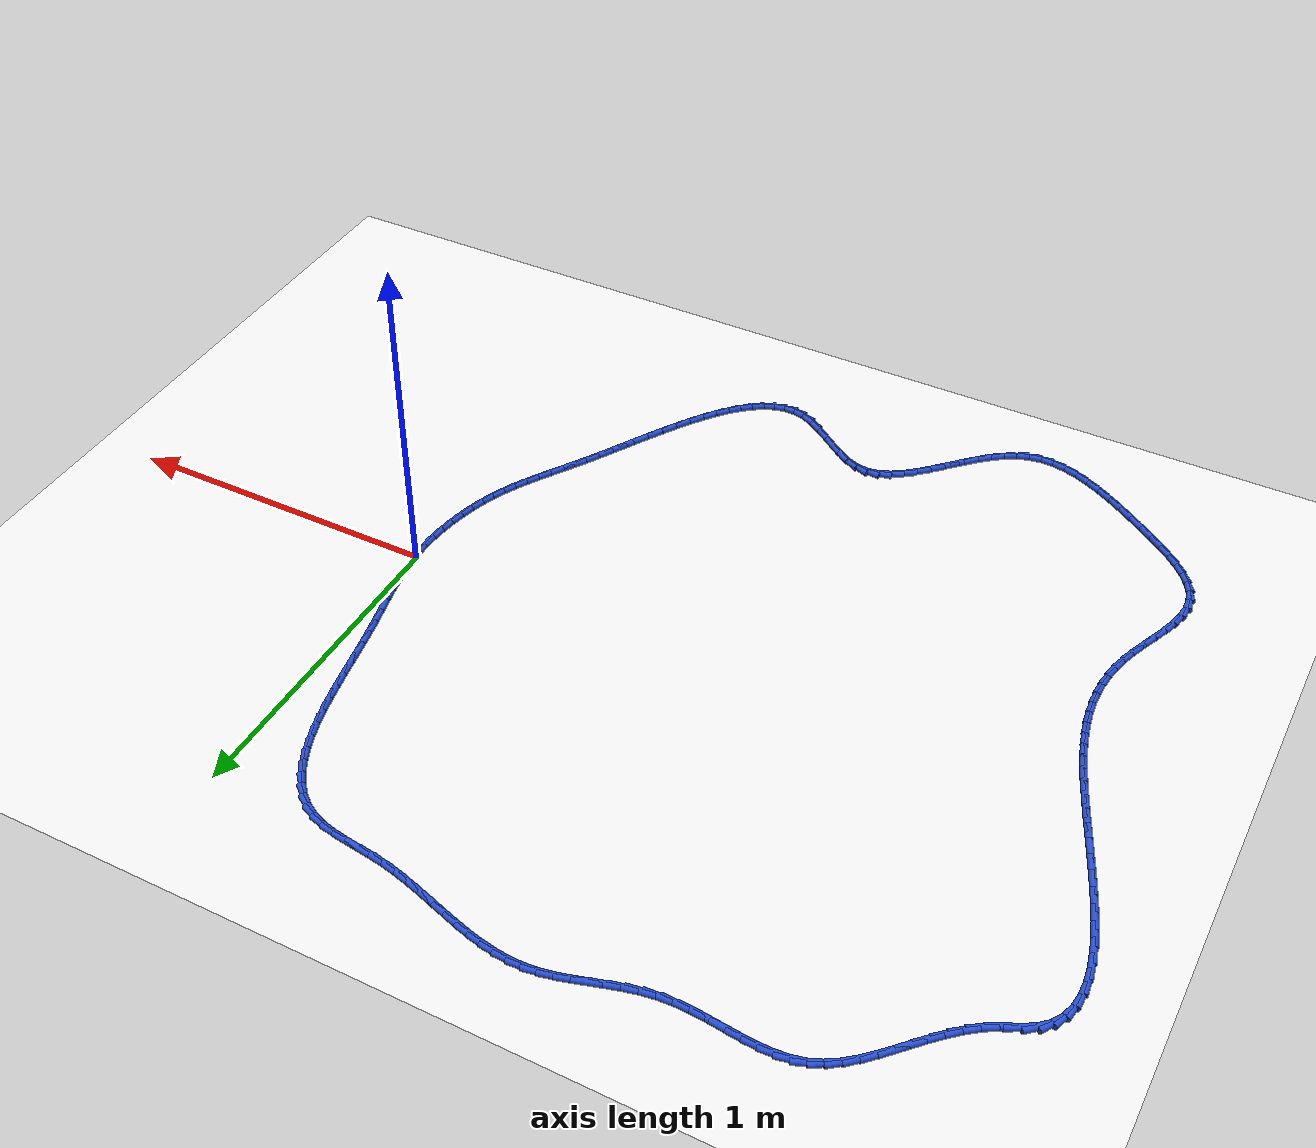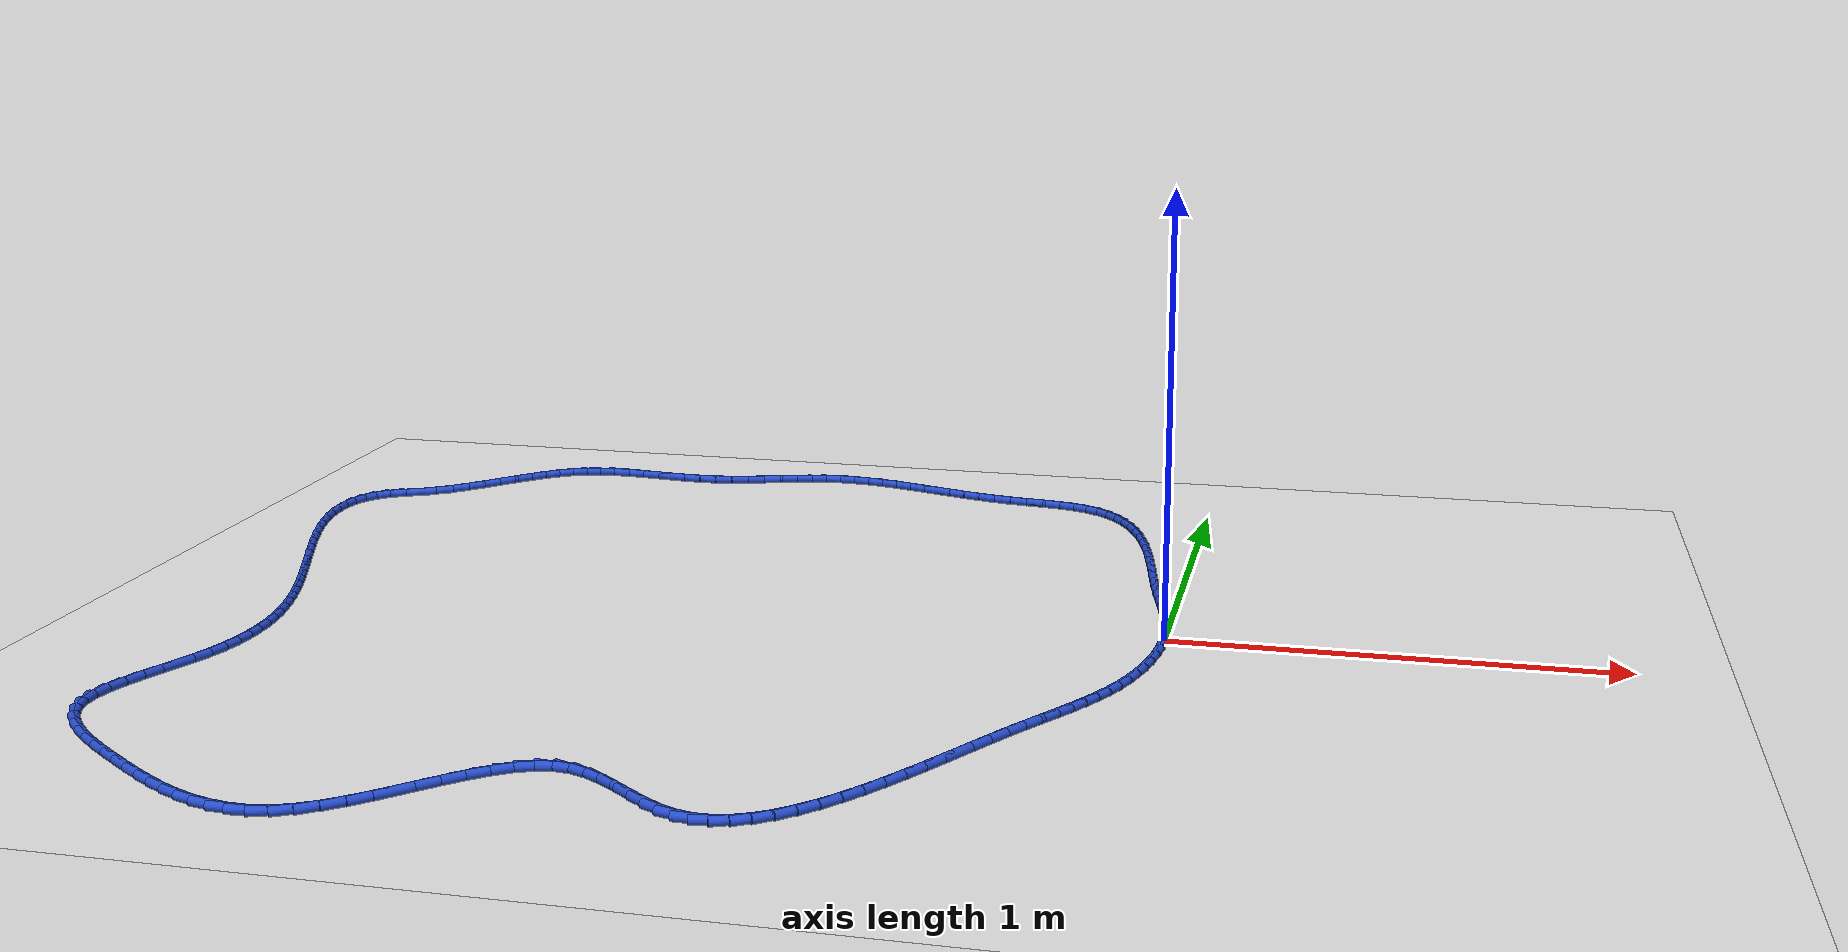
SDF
<sdf version="1.6">
 <world name="default">
  <light name="sun" type="directional">
   <pose>0 0 10 0 -0 0</pose>
   <diffuse>0.8 0.8 0.8 1</diffuse>
   <specular>0.2 0.2 0.2 1</specular>
   <attenuation>
    <range>1000</range>
    <constant>0.9</constant>
    <linear>0.01</linear>
    <quadratic>0.001</quadratic>
   </attenuation>
   <direction>-0.5 0.1 -0.9</direction>
  </light>
  <model name="ground_plane">
   <static>1</static>
   <link name="link">
    <collision name="collision">
     <geometry><plane><normal>0 0 1</normal><size>100 100</size></plane></geometry>
     <surface><friction><ode><mu>100</mu><mu2>50</mu2></ode></friction></surface>
    </collision>
    <visual name="visual">
     <cast_shadows>0</cast_shadows>
     <geometry><plane><normal>0 0 1</normal><size>100 100</size></plane></geometry>
     <material>
      <script><uri>file://media/materials/scripts/gazebo.material</uri><name>Gazebo/WhiteGlow</name></script>
     </material>
    </visual>
   </link>
  </model>
  <gravity>0 0 -9.8</gravity>
  <magnetic_field>6e-06 2.3e-05 -4.2e-05</magnetic_field>
  <atmosphere type="adiabatic"/>
  <physics name="default_physics" default="0" type="ode">
   <max_step_size>0.001</max_step_size>
   <real_time_factor>1</real_time_factor>
   <real_time_update_rate>1000</real_time_update_rate>
  </physics>
  <scene><ambient>0.4 0.4 0.4 1</ambient><background>0.7 0.7 0.7 1</background><shadows>1</shadows></scene>
  <spherical_coordinates>
   <surface_model>EARTH_WGS84</surface_model>
   <latitude_deg>0</latitude_deg>
   <longitude_deg>0</longitude_deg>
   <elevation>0</elevation>
   <heading_deg>0</heading_deg>
  </spherical_coordinates>
  <model name="line">
   <link name="link_0">
    <pose>-2.6020852139652106e-17 8.326672684688674e-17 0.01 0 1.57 -1.5039802592208182</pose>
    <collision name="collision">
     <geometry><cylinder><radius>0.01</radius><length>0.08</length></cylinder></geometry>
    </collision>
    <visual name="visual">
     <material>
      <script><name>Gazebo/Blue</name><uri>file://media/materials/scripts/gazebo.material</uri></script>
     </material>
     <geometry><cylinder><radius>0.01</radius><length>0.08</length></cylinder></geometry>
    </visual>
   </link>
   <link name="link_1">
    <pose>-0.0028225287554615574 0.042180381461454544 0.01 0 1.57 -1.4535820970283893</pose>
    <collision name="collision">
     <geometry><cylinder><radius>0.01</radius><length>0.08</length></cylinder></geometry>
    </collision>
    <visual name="visual">
     <material>
      <script><name>Gazebo/Blue</name><uri>file://media/materials/scripts/gazebo.material</uri></script>
     </material>
     <geometry><cylinder><radius>0.01</radius><length>0.08</length></cylinder></geometry>
    </visual>
   </link>
   <link name="link_2">
    <pose>-0.007724210542841146 0.08380683631250536 0.01 0 1.57 -1.4125237762256877</pose>
    <collision name="collision">
     <geometry><cylinder><radius>0.01</radius><length>0.08</length></cylinder></geometry>
    </collision>
    <visual name="visual">
     <material>
      <script><name>Gazebo/Blue</name><uri>file://media/materials/scripts/gazebo.material</uri></script>
     </material>
     <geometry><cylinder><radius>0.01</radius><length>0.08</length></cylinder></geometry>
    </visual>
   </link>
   <link name="link_3">
    <pose>-0.014328746447339006 0.12518669179951855 0.01 0 1.57 -1.3816983247495067</pose>
    <collision name="collision">
     <geometry><cylinder><radius>0.01</radius><length>0.08</length></cylinder></geometry>
    </collision>
    <visual name="visual">
     <material>
      <script><name>Gazebo/Blue</name><uri>file://media/materials/scripts/gazebo.material</uri></script>
     </material>
     <geometry><cylinder><radius>0.01</radius><length>0.08</length></cylinder></geometry>
    </visual>
   </link>
   <link name="link_4">
    <pose>-0.02225983755415534 0.1666272751688602 0.01 0 1.57 -1.361479322060791</pose>
    <collision name="collision">
     <geometry><cylinder><radius>0.01</radius><length>0.08</length></cylinder></geometry>
    </collision>
    <visual name="visual">
     <material>
      <script><name>Gazebo/Blue</name><uri>file://media/materials/scripts/gazebo.material</uri></script>
     </material>
     <geometry><cylinder><radius>0.01</radius><length>0.08</length></cylinder></geometry>
    </visual>
   </link>
   <link name="link_5">
    <pose>-0.031141184948490358 0.2084359136668963 0.01 0 1.57 -1.3518041517038408</pose>
    <collision name="collision">
     <geometry><cylinder><radius>0.01</radius><length>0.08</length></cylinder></geometry>
    </collision>
    <visual name="visual">
     <material>
      <script><name>Gazebo/Blue</name><uri>file://media/materials/scripts/gazebo.material</uri></script>
     </material>
     <geometry><cylinder><radius>0.01</radius><length>0.08</length></cylinder></geometry>
    </visual>
   </link>
   <link name="link_6">
    <pose>-0.04059648971554426 0.250919934539993 0.01 0 1.57 -1.3522657269978196</pose>
    <collision name="collision">
     <geometry><cylinder><radius>0.01</radius><length>0.08</length></cylinder></geometry>
    </collision>
    <visual name="visual">
     <material>
      <script><name>Gazebo/Blue</name><uri>file://media/materials/scripts/gazebo.material</uri></script>
     </material>
     <geometry><cylinder><radius>0.01</radius><length>0.08</length></cylinder></geometry>
    </visual>
   </link>
   <link name="link_7">
    <pose>-0.05024945294051728 0.2943866650345163 0.01 0 1.57 -1.3621911399872573</pose>
    <collision name="collision">
     <geometry><cylinder><radius>0.01</radius><length>0.08</length></cylinder></geometry>
    </collision>
    <visual name="visual">
     <material>
      <script><name>Gazebo/Blue</name><uri>file://media/materials/scripts/gazebo.material</uri></script>
     </material>
     <geometry><cylinder><radius>0.01</radius><length>0.08</length></cylinder></geometry>
    </visual>
   </link>
   <link name="link_8">
    <pose>-0.059723775708609594 0.33914343239683226 0.01 0 1.57 -1.3784438186986334</pose>
    <collision name="collision">
     <geometry><cylinder><radius>0.01</radius><length>0.08</length></cylinder></geometry>
    </collision>
    <visual name="visual">
     <material>
      <script><name>Gazebo/Blue</name><uri>file://media/materials/scripts/gazebo.material</uri></script>
     </material>
     <geometry><cylinder><radius>0.01</radius><length>0.08</length></cylinder></geometry>
    </visual>
   </link>
   <link name="link_9">
    <pose>-0.06873208378869843 0.38539670055910574 0.01 0 1.57 -1.3898341945856387</pose>
    <collision name="collision">
     <geometry><cylinder><radius>0.01</radius><length>0.08</length></cylinder></geometry>
    </collision>
    <visual name="visual">
     <material>
      <script><name>Gazebo/Blue</name><uri>file://media/materials/scripts/gazebo.material</uri></script>
     </material>
     <geometry><cylinder><radius>0.01</radius><length>0.08</length></cylinder></geometry>
    </visual>
   </link>
   <link name="link_10">
    <pose>-0.07741708040426015 0.43286511572235636 0.01 0 1.57 -1.393740418584967</pose>
    <collision name="collision">
     <geometry><cylinder><radius>0.01</radius><length>0.08</length></cylinder></geometry>
    </collision>
    <visual name="visual">
     <material>
      <script><name>Gazebo/Blue</name><uri>file://media/materials/scripts/gazebo.material</uri></script>
     </material>
     <geometry><cylinder><radius>0.01</radius><length>0.08</length></cylinder></geometry>
    </visual>
   </link>
   <link name="link_11">
    <pose>-0.08605131432259203 0.4811200460614979 0.01 0 1.57 -1.3905971796316443</pose>
    <collision name="collision">
     <geometry><cylinder><radius>0.01</radius><length>0.08</length></cylinder></geometry>
    </collision>
    <visual name="visual">
     <material>
      <script><name>Gazebo/Blue</name><uri>file://media/materials/scripts/gazebo.material</uri></script>
     </material>
     <geometry><cylinder><radius>0.01</radius><length>0.08</length></cylinder></geometry>
    </visual>
   </link>
   <link name="link_12">
    <pose>-0.0949073615439002 0.5297328288623668 0.01 0 1.57 -1.3805012895272004</pose>
    <collision name="collision">
     <geometry><cylinder><radius>0.01</radius><length>0.08</length></cylinder></geometry>
    </collision>
    <visual name="visual">
     <material>
      <script><name>Gazebo/Blue</name><uri>file://media/materials/scripts/gazebo.material</uri></script>
     </material>
     <geometry><cylinder><radius>0.01</radius><length>0.08</length></cylinder></geometry>
    </visual>
   </link>
   <link name="link_13">
    <pose>-0.10425779806839068 0.5782748014107995 0.01 0 1.57 -1.3632364919898656</pose>
    <collision name="collision">
     <geometry><cylinder><radius>0.01</radius><length>0.08</length></cylinder></geometry>
    </collision>
    <visual name="visual">
     <material>
      <script><name>Gazebo/Blue</name><uri>file://media/materials/scripts/gazebo.material</uri></script>
     </material>
     <geometry><cylinder><radius>0.01</radius><length>0.08</length></cylinder></geometry>
    </visual>
   </link>
   <link name="link_14">
    <pose>-0.11437519989626957 0.6263173009926324 0.01 0 1.57 -1.3382739933865464</pose>
    <collision name="collision">
     <geometry><cylinder><radius>0.01</radius><length>0.08</length></cylinder></geometry>
    </collision>
    <visual name="visual">
     <material>
      <script><name>Gazebo/Blue</name><uri>file://media/materials/scripts/gazebo.material</uri></script>
     </material>
     <geometry><cylinder><radius>0.01</radius><length>0.08</length></cylinder></geometry>
    </visual>
   </link>
   <link name="link_15">
    <pose>-0.1255321430277429 0.6734316648937018 0.01 0 1.57 -1.3047533090541956</pose>
    <collision name="collision">
     <geometry><cylinder><radius>0.01</radius><length>0.08</length></cylinder></geometry>
    </collision>
    <visual name="visual">
     <material>
      <script><name>Gazebo/Blue</name><uri>file://media/materials/scripts/gazebo.material</uri></script>
     </material>
     <geometry><cylinder><radius>0.01</radius><length>0.08</length></cylinder></geometry>
    </visual>
   </link>
   <link name="link_16">
    <pose>-0.1380012034630167 0.7191892303998441 0.01 0 1.57 -1.261450714936021</pose>
    <collision name="collision">
     <geometry><cylinder><radius>0.01</radius><length>0.08</length></cylinder></geometry>
    </collision>
    <visual name="visual">
     <material>
      <script><name>Gazebo/Blue</name><uri>file://media/materials/scripts/gazebo.material</uri></script>
     </material>
     <geometry><cylinder><radius>0.01</radius><length>0.08</length></cylinder></geometry>
    </visual>
   </link>
   <link name="link_17">
    <pose>-0.1520549572022971 0.763161334796896 0.01 0 1.57 -1.2067500142468197</pose>
    <collision name="collision">
     <geometry><cylinder><radius>0.01</radius><length>0.08</length></cylinder></geometry>
    </collision>
    <visual name="visual">
     <material>
      <script><name>Gazebo/Blue</name><uri>file://media/materials/scripts/gazebo.material</uri></script>
     </material>
     <geometry><cylinder><radius>0.01</radius><length>0.08</length></cylinder></geometry>
    </visual>
   </link>
   <link name="link_18">
    <pose>-0.16796598024579013 0.8049193153706937 0.01 0 1.57 -1.1386477771274877</pose>
    <collision name="collision">
     <geometry><cylinder><radius>0.01</radius><length>0.08</length></cylinder></geometry>
    </collision>
    <visual name="visual">
     <material>
      <script><name>Gazebo/Blue</name><uri>file://media/materials/scripts/gazebo.material</uri></script>
     </material>
     <geometry><cylinder><radius>0.01</radius><length>0.08</length></cylinder></geometry>
    </visual>
   </link>
   <link name="link_19">
    <pose>-0.1860068485937018 0.8440345094070736 0.01 0 1.57 -1.0548588748669203</pose>
    <collision name="collision">
     <geometry><cylinder><radius>0.01</radius><length>0.08</length></cylinder></geometry>
    </collision>
    <visual name="visual">
     <material>
      <script><name>Gazebo/Blue</name><uri>file://media/materials/scripts/gazebo.material</uri></script>
     </material>
     <geometry><cylinder><radius>0.01</radius><length>0.08</length></cylinder></geometry>
    </visual>
   </link>
   <link name="link_20">
    <pose>-0.2064501382462383 0.8800782541918724 0.01 0 1.57 -0.9531390409509436</pose>
    <collision name="collision">
     <geometry><cylinder><radius>0.01</radius><length>0.08</length></cylinder></geometry>
    </collision>
    <visual name="visual">
     <material>
      <script><name>Gazebo/Blue</name><uri>file://media/materials/scripts/gazebo.material</uri></script>
     </material>
     <geometry><cylinder><radius>0.01</radius><length>0.08</length></cylinder></geometry>
    </visual>
   </link>
   <link name="link_21">
    <pose>-0.22956842520360554 0.912621887010926 0.01 0 1.57 -0.8319804685462079</pose>
    <collision name="collision">
     <geometry><cylinder><radius>0.01</radius><length>0.08</length></cylinder></geometry>
    </collision>
    <visual name="visual">
     <material>
      <script><name>Gazebo/Blue</name><uri>file://media/materials/scripts/gazebo.material</uri></script>
     </material>
     <geometry><cylinder><radius>0.01</radius><length>0.08</length></cylinder></geometry>
    </visual>
   </link>
   <link name="link_22">
    <pose>-0.25563428546600975 0.9412367451500712 0.01 0 1.57 -0.691756756604518</pose>
    <collision name="collision">
     <geometry><cylinder><radius>0.01</radius><length>0.08</length></cylinder></geometry>
    </collision>
    <visual name="visual">
     <material>
      <script><name>Gazebo/Blue</name><uri>file://media/materials/scripts/gazebo.material</uri></script>
     </material>
     <geometry><cylinder><radius>0.01</radius><length>0.08</length></cylinder></geometry>
    </visual>
   </link>
   <link name="link_23">
    <pose>-0.2849202950336569 0.9654941658951444 0.01 0 1.57 -0.5360130160347677</pose>
    <collision name="collision">
     <geometry><cylinder><radius>0.01</radius><length>0.08</length></cylinder></geometry>
    </collision>
    <visual name="visual">
     <material>
      <script><name>Gazebo/Blue</name><uri>file://media/materials/scripts/gazebo.material</uri></script>
     </material>
     <geometry><cylinder><radius>0.01</radius><length>0.08</length></cylinder></geometry>
    </visual>
   </link>
   <link name="link_24">
    <pose>-0.31769902990675286 0.9849654865319818 0.01 0 1.57 -0.3739385669005846</pose>
    <collision name="collision">
     <geometry><cylinder><radius>0.01</radius><length>0.08</length></cylinder></geometry>
    </collision>
    <visual name="visual">
     <material>
      <script><name>Gazebo/Blue</name><uri>file://media/materials/scripts/gazebo.material</uri></script>
     </material>
     <geometry><cylinder><radius>0.01</radius><length>0.08</length></cylinder></geometry>
    </visual>
   </link>
   <link name="link_25">
    <pose>-0.35420394141933365 0.9992900573927145 0.01 0 1.57 -0.24272672618426147</pose>
    <collision name="collision">
     <geometry><cylinder><radius>0.01</radius><length>0.08</length></cylinder></geometry>
    </collision>
    <visual name="visual">
     <material>
      <script><name>Gazebo/Blue</name><uri>file://media/materials/scripts/gazebo.material</uri></script>
     </material>
     <geometry><cylinder><radius>0.01</radius><length>0.08</length></cylinder></geometry>
    </visual>
   </link>
   <link name="link_26">
    <pose>-0.3940631367904359 1.0091595393170696 0.01 0 1.57 -0.1622385226868523</pose>
    <collision name="collision">
     <geometry><cylinder><radius>0.01</radius><length>0.08</length></cylinder></geometry>
    </collision>
    <visual name="visual">
     <material>
      <script><name>Gazebo/Blue</name><uri>file://media/materials/scripts/gazebo.material</uri></script>
     </material>
     <geometry><cylinder><radius>0.01</radius><length>0.08</length></cylinder></geometry>
    </visual>
   </link>
   <link name="link_27">
    <pose>-0.4364283235287667 1.0160937508960022 0.01 0 1.57 -0.12524716902368274</pose>
    <collision name="collision">
     <geometry><cylinder><radius>0.01</radius><length>0.08</length></cylinder></geometry>
    </collision>
    <visual name="visual">
     <material>
      <script><name>Gazebo/Blue</name><uri>file://media/materials/scripts/gazebo.material</uri></script>
     </material>
     <geometry><cylinder><radius>0.01</radius><length>0.08</length></cylinder></geometry>
    </visual>
   </link>
   <link name="link_28">
    <pose>-0.48043833811379344 1.02163488529879 0.01 0 1.57 -0.1263556645864961</pose>
    <collision name="collision">
     <geometry><cylinder><radius>0.01</radius><length>0.08</length></cylinder></geometry>
    </collision>
    <visual name="visual">
     <material>
      <script><name>Gazebo/Blue</name><uri>file://media/materials/scripts/gazebo.material</uri></script>
     </material>
     <geometry><cylinder><radius>0.01</radius><length>0.08</length></cylinder></geometry>
    </visual>
   </link>
   <link name="link_29">
    <pose>-0.5252320170249823 1.0273251356947102 0.01 0 1.57 -0.16312141012108544</pose>
    <collision name="collision">
     <geometry><cylinder><radius>0.01</radius><length>0.08</length></cylinder></geometry>
    </collision>
    <visual name="visual">
     <material>
      <script><name>Gazebo/Blue</name><uri>file://media/materials/scripts/gazebo.material</uri></script>
     </material>
     <geometry><cylinder><radius>0.01</radius><length>0.08</length></cylinder></geometry>
    </visual>
   </link>
   <link name="link_30">
    <pose>-0.5699569184042637 1.034686129350251 0.01 0 1.57 -0.2158428964799083</pose>
    <collision name="collision">
     <geometry><cylinder><radius>0.01</radius><length>0.08</length></cylinder></geometry>
    </collision>
    <visual name="visual">
     <material>
      <script><name>Gazebo/Blue</name><uri>file://media/materials/scripts/gazebo.material</uri></script>
     </material>
     <geometry><cylinder><radius>0.01</radius><length>0.08</length></cylinder></geometry>
    </visual>
   </link>
   <link name="link_31">
    <pose>-0.6141288314327578 1.0443711953389343 0.01 0 1.57 -0.2575652141031595</pose>
    <collision name="collision">
     <geometry><cylinder><radius>0.01</radius><length>0.08</length></cylinder></geometry>
    </collision>
    <visual name="visual">
     <material>
      <script><name>Gazebo/Blue</name><uri>file://media/materials/scripts/gazebo.material</uri></script>
     </material>
     <geometry><cylinder><radius>0.01</radius><length>0.08</length></cylinder></geometry>
    </visual>
   </link>
   <link name="link_32">
    <pose>-0.6577594891147347 1.0558642145356778 0.01 0 1.57 -0.2863775817328964</pose>
    <collision name="collision">
     <geometry><cylinder><radius>0.01</radius><length>0.08</length></cylinder></geometry>
    </collision>
    <visual name="visual">
     <material>
      <script><name>Gazebo/Blue</name><uri>file://media/materials/scripts/gazebo.material</uri></script>
     </material>
     <geometry><cylinder><radius>0.01</radius><length>0.08</length></cylinder></geometry>
    </visual>
   </link>
   <link name="link_33">
    <pose>-0.70089560065749 1.0685665930355683 0.01 0 1.57 -0.30230978403218756</pose>
    <collision name="collision">
     <geometry><cylinder><radius>0.01</radius><length>0.08</length></cylinder></geometry>
    </collision>
    <visual name="visual">
     <material>
      <script><name>Gazebo/Blue</name><uri>file://media/materials/scripts/gazebo.material</uri></script>
     </material>
     <geometry><cylinder><radius>0.01</radius><length>0.08</length></cylinder></geometry>
    </visual>
   </link>
   <link name="link_34">
    <pose>-0.7435838752683188 1.0818797369336928 0.01 0 1.57 -0.30526546400296256</pose>
    <collision name="collision">
     <geometry><cylinder><radius>0.01</radius><length>0.08</length></cylinder></geometry>
    </collision>
    <visual name="visual">
     <material>
      <script><name>Gazebo/Blue</name><uri>file://media/materials/scripts/gazebo.material</uri></script>
     </material>
     <geometry><cylinder><radius>0.01</radius><length>0.08</length></cylinder></geometry>
    </visual>
   </link>
   <link name="link_35">
    <pose>-0.7858710221545171 1.0952050523251387 0.01 0 1.57 -0.29493348396031016</pose>
    <collision name="collision">
     <geometry><cylinder><radius>0.01</radius><length>0.08</length></cylinder></geometry>
    </collision>
    <visual name="visual">
     <material>
      <script><name>Gazebo/Blue</name><uri>file://media/materials/scripts/gazebo.material</uri></script>
     </material>
     <geometry><cylinder><radius>0.01</radius><length>0.08</length></cylinder></geometry>
    </visual>
   </link>
   <link name="link_36">
    <pose>-0.8278037505233797 1.107943945304991 0.01 0 1.57 -0.2707543948793274</pose>
    <collision name="collision">
     <geometry><cylinder><radius>0.01</radius><length>0.08</length></cylinder></geometry>
    </collision>
    <visual name="visual">
     <material>
      <script><name>Gazebo/Blue</name><uri>file://media/materials/scripts/gazebo.material</uri></script>
     </material>
     <geometry><cylinder><radius>0.01</radius><length>0.08</length></cylinder></geometry>
    </visual>
   </link>
   <link name="link_37">
    <pose>-0.8694287695822028 1.119497821968339 0.01 0 1.57 -0.23195080442011196</pose>
    <collision name="collision">
     <geometry><cylinder><radius>0.01</radius><length>0.08</length></cylinder></geometry>
    </collision>
    <visual name="visual">
     <material>
      <script><name>Gazebo/Blue</name><uri>file://media/materials/scripts/gazebo.material</uri></script>
     </material>
     <geometry><cylinder><radius>0.01</radius><length>0.08</length></cylinder></geometry>
    </visual>
   </link>
   <link name="link_38">
    <pose>-0.9107927885382815 1.1292680884102682 0.01 0 1.57 -0.1776482837785822</pose>
    <collision name="collision">
     <geometry><cylinder><radius>0.01</radius><length>0.08</length></cylinder></geometry>
    </collision>
    <visual name="visual">
     <material>
      <script><name>Gazebo/Blue</name><uri>file://media/materials/scripts/gazebo.material</uri></script>
     </material>
     <geometry><cylinder><radius>0.01</radius><length>0.08</length></cylinder></geometry>
    </visual>
   </link>
   <link name="link_39">
    <pose>-0.9519425165989112 1.1366561507258657 0.01 0 1.57 -0.10712935939208024</pose>
    <collision name="collision">
     <geometry><cylinder><radius>0.01</radius><length>0.08</length></cylinder></geometry>
    </collision>
    <visual name="visual">
     <material>
      <script><name>Gazebo/Blue</name><uri>file://media/materials/scripts/gazebo.material</uri></script>
     </material>
     <geometry><cylinder><radius>0.01</radius><length>0.08</length></cylinder></geometry>
    </visual>
   </link>
   <link name="link_40">
    <pose>-0.9929246629713877 1.1410634150102186 0.01 0 1.57 -0.020257789818603874</pose>
    <collision name="collision">
     <geometry><cylinder><radius>0.01</radius><length>0.08</length></cylinder></geometry>
    </collision>
    <visual name="visual">
     <material>
      <script><name>Gazebo/Blue</name><uri>file://media/materials/scripts/gazebo.material</uri></script>
     </material>
     <geometry><cylinder><radius>0.01</radius><length>0.08</length></cylinder></geometry>
    </visual>
   </link>
   <link name="link_41">
    <pose>-1.0337859368630058 1.1418912873584133 0.01 0 1.57 0.08189680555741315</pose>
    <collision name="collision">
     <geometry><cylinder><radius>0.01</radius><length>0.08</length></cylinder></geometry>
    </collision>
    <visual name="visual">
     <material>
      <script><name>Gazebo/Blue</name><uri>file://media/materials/scripts/gazebo.material</uri></script>
     </material>
     <geometry><cylinder><radius>0.01</radius><length>0.08</length></cylinder></geometry>
    </visual>
   </link>
   <link name="link_42">
    <pose>-1.074573151165025 1.1385434567204546 0.01 0 1.57 0.18410774424874166</pose>
    <collision name="collision">
     <geometry><cylinder><radius>0.01</radius><length>0.08</length></cylinder></geometry>
    </collision>
    <visual name="visual">
     <material>
      <script><name>Gazebo/Blue</name><uri>file://media/materials/scripts/gazebo.material</uri></script>
     </material>
     <geometry><cylinder><radius>0.01</radius><length>0.08</length></cylinder></geometry>
    </visual>
   </link>
   <link name="link_43">
    <pose>-1.1153569736976783 1.1309488363957154 0.01 0 1.57 0.256298369105912</pose>
    <collision name="collision">
     <geometry><cylinder><radius>0.01</radius><length>0.08</length></cylinder></geometry>
    </collision>
    <visual name="visual">
     <material>
      <script><name>Gazebo/Blue</name><uri>file://media/materials/scripts/gazebo.material</uri></script>
     </material>
     <geometry><cylinder><radius>0.01</radius><length>0.08</length></cylinder></geometry>
    </visual>
   </link>
   <link name="link_44">
    <pose>-1.156262246878765 1.1202291253668561 0.01 0 1.57 0.2961466587748973</pose>
    <collision name="collision">
     <geometry><cylinder><radius>0.01</radius><length>0.08</length></cylinder></geometry>
    </collision>
    <visual name="visual">
     <material>
      <script><name>Gazebo/Blue</name><uri>file://media/materials/scripts/gazebo.material</uri></script>
     </material>
     <geometry><cylinder><radius>0.01</radius><length>0.08</length></cylinder></geometry>
    </visual>
   </link>
   <link name="link_45">
    <pose>-1.1974212930094799 1.1076707104634085 0.01 0 1.57 0.3056865476496799</pose>
    <collision name="collision">
     <geometry><cylinder><radius>0.01</radius><length>0.08</length></cylinder></geometry>
    </collision>
    <visual name="visual">
     <material>
      <script><name>Gazebo/Blue</name><uri>file://media/materials/scripts/gazebo.material</uri></script>
     </material>
     <geometry><cylinder><radius>0.01</radius><length>0.08</length></cylinder></geometry>
    </visual>
   </link>
   <link name="link_46">
    <pose>-1.2389664343910192 1.0945599785149045 0.01 0 1.57 0.2861614366990151</pose>
    <collision name="collision">
     <geometry><cylinder><radius>0.01</radius><length>0.08</length></cylinder></geometry>
    </collision>
    <visual name="visual">
     <material>
      <script><name>Gazebo/Blue</name><uri>file://media/materials/scripts/gazebo.material</uri></script>
     </material>
     <geometry><cylinder><radius>0.01</radius><length>0.08</length></cylinder></geometry>
    </visual>
   </link>
   <link name="link_47">
    <pose>-1.2810299933245772 1.0821833163508756 0.01 0 1.57 0.23786299277136586</pose>
    <collision name="collision">
     <geometry><cylinder><radius>0.01</radius><length>0.08</length></cylinder></geometry>
    </collision>
    <visual name="visual">
     <material>
      <script><name>Gazebo/Blue</name><uri>file://media/materials/scripts/gazebo.material</uri></script>
     </material>
     <geometry><cylinder><radius>0.01</radius><length>0.08</length></cylinder></geometry>
    </visual>
   </link>
   <link name="link_48">
    <pose>-1.32374429211135 1.0718271108008544 0.01 0 1.57 0.16066722216159088</pose>
    <collision name="collision">
     <geometry><cylinder><radius>0.01</radius><length>0.08</length></cylinder></geometry>
    </collision>
    <visual name="visual">
     <material>
      <script><name>Gazebo/Blue</name><uri>file://media/materials/scripts/gazebo.material</uri></script>
     </material>
     <geometry><cylinder><radius>0.01</radius><length>0.08</length></cylinder></geometry>
    </visual>
   </link>
   <link name="link_49">
    <pose>-1.367241653052532 1.0647777486943713 0.01 0 1.57 0.06099022538829343</pose>
    <collision name="collision">
     <geometry><cylinder><radius>0.01</radius><length>0.08</length></cylinder></geometry>
    </collision>
    <visual name="visual">
     <material>
      <script><name>Gazebo/Blue</name><uri>file://media/materials/scripts/gazebo.material</uri></script>
     </material>
     <geometry><cylinder><radius>0.01</radius><length>0.08</length></cylinder></geometry>
    </visual>
   </link>
   <link name="link_50">
    <pose>-1.4116028810396957 1.0620687876296848 0.01 0 1.57 -0.02235480627939234</pose>
    <collision name="collision">
     <geometry><cylinder><radius>0.01</radius><length>0.08</length></cylinder></geometry>
    </collision>
    <visual name="visual">
     <material>
      <script><name>Gazebo/Blue</name><uri>file://media/materials/scripts/gazebo.material</uri></script>
     </material>
     <geometry><cylinder><radius>0.01</radius><length>0.08</length></cylinder></geometry>
    </visual>
   </link>
   <link name="link_51">
    <pose>-1.4565706178410716 1.0630742001610183 0.01 0 1.57 -0.07565118614138357</pose>
    <collision name="collision">
     <geometry><cylinder><radius>0.01</radius><length>0.08</length></cylinder></geometry>
    </collision>
    <visual name="visual">
     <material>
      <script><name>Gazebo/Blue</name><uri>file://media/materials/scripts/gazebo.material</uri></script>
     </material>
     <geometry><cylinder><radius>0.01</radius><length>0.08</length></cylinder></geometry>
    </visual>
   </link>
   <link name="link_52">
    <pose>-1.5017511336101488 1.066498695174736 0.01 0 1.57 -0.10069201604670874</pose>
    <collision name="collision">
     <geometry><cylinder><radius>0.01</radius><length>0.08</length></cylinder></geometry>
    </collision>
    <visual name="visual">
     <material>
      <script><name>Gazebo/Blue</name><uri>file://media/materials/scripts/gazebo.material</uri></script>
     </material>
     <geometry><cylinder><radius>0.01</radius><length>0.08</length></cylinder></geometry>
    </visual>
   </link>
   <link name="link_53">
    <pose>-1.5467503211675309 1.071045129740832 0.01 0 1.57 -0.09808277241048377</pose>
    <collision name="collision">
     <geometry><cylinder><radius>0.01</radius><length>0.08</length></cylinder></geometry>
    </collision>
    <visual name="visual">
     <material>
      <script><name>Gazebo/Blue</name><uri>file://media/materials/scripts/gazebo.material</uri></script>
     </material>
     <geometry><cylinder><radius>0.01</radius><length>0.08</length></cylinder></geometry>
    </visual>
   </link>
   <link name="link_54">
    <pose>-1.5911740733338242 1.0754163609293022 0.01 0 1.57 -0.06661255522651933</pose>
    <collision name="collision">
     <geometry><cylinder><radius>0.01</radius><length>0.08</length></cylinder></geometry>
    </collision>
    <visual name="visual">
     <material>
      <script><name>Gazebo/Blue</name><uri>file://media/materials/scripts/gazebo.material</uri></script>
     </material>
     <geometry><cylinder><radius>0.01</radius><length>0.08</length></cylinder></geometry>
    </visual>
   </link>
   <link name="link_55">
    <pose>-1.6346282829296348 1.0783152458101406 0.01 0 1.57 -0.0030742103703682885</pose>
    <collision name="collision">
     <geometry><cylinder><radius>0.01</radius><length>0.08</length></cylinder></geometry>
    </collision>
    <visual name="visual">
     <material>
      <script><name>Gazebo/Blue</name><uri>file://media/materials/scripts/gazebo.material</uri></script>
     </material>
     <geometry><cylinder><radius>0.01</radius><length>0.08</length></cylinder></geometry>
    </visual>
   </link>
   <link name="link_56">
    <pose>-1.6767188427755668 1.0784446414533433 0.01 0 1.57 0.09731039615867956</pose>
    <collision name="collision">
     <geometry><cylinder><radius>0.01</radius><length>0.08</length></cylinder></geometry>
    </collision>
    <visual name="visual">
     <material>
      <script><name>Gazebo/Blue</name><uri>file://media/materials/scripts/gazebo.material</uri></script>
     </material>
     <geometry><cylinder><radius>0.01</radius><length>0.08</length></cylinder></geometry>
    </visual>
   </link>
   <link name="link_57">
    <pose>-1.7170516456922265 1.074507404928904 0.01 0 1.57 0.23894945844731774</pose>
    <collision name="collision">
     <geometry><cylinder><radius>0.01</radius><length>0.08</length></cylinder></geometry>
    </collision>
    <visual name="visual">
     <material>
      <script><name>Gazebo/Blue</name><uri>file://media/materials/scripts/gazebo.material</uri></script>
     </material>
     <geometry><cylinder><radius>0.01</radius><length>0.08</length></cylinder></geometry>
    </visual>
   </link>
   <link name="link_58">
    <pose>-1.7552325845002201 1.0652063933068188 0.01 0 1.57 0.41126925163174294</pose>
    <collision name="collision">
     <geometry><cylinder><radius>0.01</radius><length>0.08</length></cylinder></geometry>
    </collision>
    <visual name="visual">
     <material>
      <script><name>Gazebo/Blue</name><uri>file://media/materials/scripts/gazebo.material</uri></script>
     </material>
     <geometry><cylinder><radius>0.01</radius><length>0.08</length></cylinder></geometry>
    </visual>
   </link>
   <link name="link_59">
    <pose>-1.7910038839021345 1.0496050609742291 0.01 0 1.57 0.5626519368448563</pose>
    <collision name="collision">
     <geometry><cylinder><radius>0.01</radius><length>0.08</length></cylinder></geometry>
    </collision>
    <visual name="visual">
     <material>
      <script><name>Gazebo/Blue</name><uri>file://media/materials/scripts/gazebo.material</uri></script>
     </material>
     <geometry><cylinder><radius>0.01</radius><length>0.08</length></cylinder></geometry>
    </visual>
   </link>
   <link name="link_60">
    <pose>-1.824706500268398 1.0283505053368704 0.01 0 1.57 0.6769133172809165</pose>
    <collision name="collision">
     <geometry><cylinder><radius>0.01</radius><length>0.08</length></cylinder></geometry>
    </collision>
    <visual name="visual">
     <material>
      <script><name>Gazebo/Blue</name><uri>file://media/materials/scripts/gazebo.material</uri></script>
     </material>
     <geometry><cylinder><radius>0.01</radius><length>0.08</length></cylinder></geometry>
    </visual>
   </link>
   <link name="link_61">
    <pose>-1.8568457059868546 1.0025244390510215 0.01 0 1.57 0.7561795019125378</pose>
    <collision name="collision">
     <geometry><cylinder><radius>0.01</radius><length>0.08</length></cylinder></geometry>
    </collision>
    <visual name="visual">
     <material>
      <script><name>Gazebo/Blue</name><uri>file://media/materials/scripts/gazebo.material</uri></script>
     </material>
     <geometry><cylinder><radius>0.01</radius><length>0.08</length></cylinder></geometry>
    </visual>
   </link>
   <link name="link_62">
    <pose>-1.8879267779651037 0.9732085867276938 0.01 0 1.57 0.80460315474322</pose>
    <collision name="collision">
     <geometry><cylinder><radius>0.01</radius><length>0.08</length></cylinder></geometry>
    </collision>
    <visual name="visual">
     <material>
      <script><name>Gazebo/Blue</name><uri>file://media/materials/scripts/gazebo.material</uri></script>
     </material>
     <geometry><cylinder><radius>0.01</radius><length>0.08</length></cylinder></geometry>
    </visual>
   </link>
   <link name="link_63">
    <pose>-1.9184549931107442 0.9414846729778992 0.01 0 1.57 0.8258228394307588</pose>
    <collision name="collision">
     <geometry><cylinder><radius>0.01</radius><length>0.08</length></cylinder></geometry>
    </collision>
    <visual name="visual">
     <material>
      <script><name>Gazebo/Blue</name><uri>file://media/materials/scripts/gazebo.material</uri></script>
     </material>
     <geometry><cylinder><radius>0.01</radius><length>0.08</length></cylinder></geometry>
    </visual>
   </link>
   <link name="link_64">
    <pose>-1.9489356283313743 0.90843442241265 0.01 0 1.57 0.822068831382171</pose>
    <collision name="collision">
     <geometry><cylinder><radius>0.01</radius><length>0.08</length></cylinder></geometry>
    </collision>
    <visual name="visual">
     <material>
      <script><name>Gazebo/Blue</name><uri>file://media/materials/scripts/gazebo.material</uri></script>
     </material>
     <geometry><cylinder><radius>0.01</radius><length>0.08</length></cylinder></geometry>
    </visual>
   </link>
   <link name="link_65">
    <pose>-1.9798739605345936 0.8751395596429579 0.01 0 1.57 0.7940438837642151</pose>
    <collision name="collision">
     <geometry><cylinder><radius>0.01</radius><length>0.08</length></cylinder></geometry>
    </collision>
    <visual name="visual">
     <material>
      <script><name>Gazebo/Blue</name><uri>file://media/materials/scripts/gazebo.material</uri></script>
     </material>
     <geometry><cylinder><radius>0.01</radius><length>0.08</length></cylinder></geometry>
    </visual>
   </link>
   <link name="link_66">
    <pose>-2.0117752666280015 0.8426818092798342 0.01 0 1.57 0.7411349434529477</pose>
    <collision name="collision">
     <geometry><cylinder><radius>0.01</radius><length>0.08</length></cylinder></geometry>
    </collision>
    <visual name="visual">
     <material>
      <script><name>Gazebo/Blue</name><uri>file://media/materials/scripts/gazebo.material</uri></script>
     </material>
     <geometry><cylinder><radius>0.01</radius><length>0.08</length></cylinder></geometry>
    </visual>
   </link>
   <link name="link_67">
    <pose>-2.0451448235191965 0.8121428959342915 0.01 0 1.57 0.6619114624031508</pose>
    <collision name="collision">
     <geometry><cylinder><radius>0.01</radius><length>0.08</length></cylinder></geometry>
    </collision>
    <visual name="visual">
     <material>
      <script><name>Gazebo/Blue</name><uri>file://media/materials/scripts/gazebo.material</uri></script>
     </material>
     <geometry><cylinder><radius>0.01</radius><length>0.08</length></cylinder></geometry>
    </visual>
   </link>
   <link name="link_68">
    <pose>-2.080487908115778 0.7846045442173416 0.01 0 1.57 0.5551197454959811</pose>
    <collision name="collision">
     <geometry><cylinder><radius>0.01</radius><length>0.08</length></cylinder></geometry>
    </collision>
    <visual name="visual">
     <material>
      <script><name>Gazebo/Blue</name><uri>file://media/materials/scripts/gazebo.material</uri></script>
     </material>
     <geometry><cylinder><radius>0.01</radius><length>0.08</length></cylinder></geometry>
    </visual>
   </link>
   <link name="link_69">
    <pose>-2.1183097973253444 0.7611484787399956 0.01 0 1.57 0.45629590736237746</pose>
    <collision name="collision">
     <geometry><cylinder><radius>0.01</radius><length>0.08</length></cylinder></geometry>
    </collision>
    <visual name="visual">
     <material>
      <script><name>Gazebo/Blue</name><uri>file://media/materials/scripts/gazebo.material</uri></script>
     </material>
     <geometry><cylinder><radius>0.01</radius><length>0.08</length></cylinder></geometry>
    </visual>
   </link>
   <link name="link_70">
    <pose>-2.1579637086260437 0.741684599671298 0.01 0 1.57 0.5141733736077727</pose>
    <collision name="collision">
     <geometry><cylinder><radius>0.01</radius><length>0.08</length></cylinder></geometry>
    </collision>
    <visual name="visual">
     <material>
      <script><name>Gazebo/Blue</name><uri>file://media/materials/scripts/gazebo.material</uri></script>
     </material>
     <geometry><cylinder><radius>0.01</radius><length>0.08</length></cylinder></geometry>
    </visual>
   </link>
   <link name="link_71">
    <pose>-2.1940584127165534 0.721296480224273 0.01 0 1.57 0.746256488153996</pose>
    <collision name="collision">
     <geometry><cylinder><radius>0.01</radius><length>0.08</length></cylinder></geometry>
    </collision>
    <visual name="visual">
     <material>
      <script><name>Gazebo/Blue</name><uri>file://media/materials/scripts/gazebo.material</uri></script>
     </material>
     <geometry><cylinder><radius>0.01</radius><length>0.08</length></cylinder></geometry>
    </visual>
   </link>
   <link name="link_72">
    <pose>-2.2218799956095565 0.6955718565646939 0.01 0 1.57 1.0084616936559099</pose>
    <collision name="collision">
     <geometry><cylinder><radius>0.01</radius><length>0.08</length></cylinder></geometry>
    </collision>
    <visual name="visual">
     <material>
      <script><name>Gazebo/Blue</name><uri>file://media/materials/scripts/gazebo.material</uri></script>
     </material>
     <geometry><cylinder><radius>0.01</radius><length>0.08</length></cylinder></geometry>
    </visual>
   </link>
   <link name="link_73">
    <pose>-2.2414753884733436 0.6644782553779486 0.01 0 1.57 1.2437995581526191</pose>
    <collision name="collision">
     <geometry><cylinder><radius>0.01</radius><length>0.08</length></cylinder></geometry>
    </collision>
    <visual name="visual">
     <material>
      <script><name>Gazebo/Blue</name><uri>file://media/materials/scripts/gazebo.material</uri></script>
     </material>
     <geometry><cylinder><radius>0.01</radius><length>0.08</length></cylinder></geometry>
    </visual>
   </link>
   <link name="link_74">
    <pose>-2.253624733980415 0.6286577291481376 0.01 0 1.57 1.4342405121999162</pose>
    <collision name="collision">
     <geometry><cylinder><radius>0.01</radius><length>0.08</length></cylinder></geometry>
    </collision>
    <visual name="visual">
     <material>
      <script><name>Gazebo/Blue</name><uri>file://media/materials/scripts/gazebo.material</uri></script>
     </material>
     <geometry><cylinder><radius>0.01</radius><length>0.08</length></cylinder></geometry>
    </visual>
   </link>
   <link name="link_75">
    <pose>-2.25910817480327 0.5887523303593616 0.01 0 1.57 -1.5615154463327876</pose>
    <collision name="collision">
     <geometry><cylinder><radius>0.01</radius><length>0.08</length></cylinder></geometry>
    </collision>
    <visual name="visual">
     <material>
      <script><name>Gazebo/Blue</name><uri>file://media/materials/scripts/gazebo.material</uri></script>
     </material>
     <geometry><cylinder><radius>0.01</radius><length>0.08</length></cylinder></geometry>
    </visual>
   </link>
   <link name="link_76">
    <pose>-2.2587058536144076 0.5454041114957212 0.01 0 1.57 -1.4520069624338265</pose>
    <collision name="collision">
     <geometry><cylinder><radius>0.01</radius><length>0.08</length></cylinder></geometry>
    </collision>
    <visual name="visual">
     <material>
      <script><name>Gazebo/Blue</name><uri>file://media/materials/scripts/gazebo.material</uri></script>
     </material>
     <geometry><cylinder><radius>0.01</radius><length>0.08</length></cylinder></geometry>
    </visual>
   </link>
   <link name="link_77">
    <pose>-2.2531979130863276 0.4992551250413159 0.01 0 1.57 -1.3699820038322505</pose>
    <collision name="collision">
     <geometry><cylinder><radius>0.01</radius><length>0.08</length></cylinder></geometry>
    </collision>
    <visual name="visual">
     <material>
      <script><name>Gazebo/Blue</name><uri>file://media/materials/scripts/gazebo.material</uri></script>
     </material>
     <geometry><cylinder><radius>0.01</radius><length>0.08</length></cylinder></geometry>
    </visual>
   </link>
   <link name="link_78">
    <pose>-2.2433644958915293 0.4509474234802474 0.01 0 1.57 -1.3084660745493457</pose>
    <collision name="collision">
     <geometry><cylinder><radius>0.01</radius><length>0.08</length></cylinder></geometry>
    </collision>
    <visual name="visual">
     <material>
      <script><name>Gazebo/Blue</name><uri>file://media/materials/scripts/gazebo.material</uri></script>
     </material>
     <geometry><cylinder><radius>0.01</radius><length>0.08</length></cylinder></geometry>
    </visual>
   </link>
   <link name="link_79">
    <pose>-2.2299857447025127 0.40112305929661574 0.01 0 1.57 -1.2625205578888958</pose>
    <collision name="collision">
     <geometry><cylinder><radius>0.01</radius><length>0.08</length></cylinder></geometry>
    </collision>
    <visual name="visual">
     <material>
      <script><name>Gazebo/Blue</name><uri>file://media/materials/scripts/gazebo.material</uri></script>
     </material>
     <geometry><cylinder><radius>0.01</radius><length>0.08</length></cylinder></geometry>
    </visual>
   </link>
   <link name="link_80">
    <pose>-2.2138418021917765 0.3504240849745206 0.01 0 1.57 -1.2288322317570486</pose>
    <collision name="collision">
     <geometry><cylinder><radius>0.01</radius><length>0.08</length></cylinder></geometry>
    </collision>
    <visual name="visual">
     <material>
      <script><name>Gazebo/Blue</name><uri>file://media/materials/scripts/gazebo.material</uri></script>
     </material>
     <geometry><cylinder><radius>0.01</radius><length>0.08</length></cylinder></geometry>
    </visual>
   </link>
   <link name="link_81">
    <pose>-2.195712811031821 0.2994925529980636 0.01 0 1.57 -1.2053074245564241</pose>
    <collision name="collision">
     <geometry><cylinder><radius>0.01</radius><length>0.08</length></cylinder></geometry>
    </collision>
    <visual name="visual">
     <material>
      <script><name>Gazebo/Blue</name><uri>file://media/materials/scripts/gazebo.material</uri></script>
     </material>
     <geometry><cylinder><radius>0.01</radius><length>0.08</length></cylinder></geometry>
    </visual>
   </link>
   <link name="link_82">
    <pose>-2.176378913895146 0.24897051585134464 0.01 0 1.57 -1.1907591544788212</pose>
    <collision name="collision">
     <geometry><cylinder><radius>0.01</radius><length>0.08</length></cylinder></geometry>
    </collision>
    <visual name="visual">
     <material>
      <script><name>Gazebo/Blue</name><uri>file://media/materials/scripts/gazebo.material</uri></script>
     </material>
     <geometry><cylinder><radius>0.01</radius><length>0.08</length></cylinder></geometry>
    </visual>
   </link>
   <link name="link_83">
    <pose>-2.1566149815928974 0.19949337447885745 0.01 0 1.57 -1.182815162359199</pose>
    <collision name="collision">
     <geometry><cylinder><radius>0.01</radius><length>0.08</length></cylinder></geometry>
    </collision>
    <visual name="visual">
     <material>
      <script><name>Gazebo/Blue</name><uri>file://media/materials/scripts/gazebo.material</uri></script>
     </material>
     <geometry><cylinder><radius>0.01</radius><length>0.08</length></cylinder></geometry>
    </visual>
   </link>
   <link name="link_84">
    <pose>-2.136957776661934 0.15139610716389426 0.01 0 1.57 -1.1788448320219596</pose>
    <collision name="collision">
     <geometry><cylinder><radius>0.01</radius><length>0.08</length></cylinder></geometry>
    </collision>
    <visual name="visual">
     <material>
      <script><name>Gazebo/Blue</name><uri>file://media/materials/scripts/gazebo.material</uri></script>
     </material>
     <geometry><cylinder><radius>0.01</radius><length>0.08</length></cylinder></geometry>
    </visual>
   </link>
   <link name="link_85">
    <pose>-2.117614067129772 0.10459733610562819 0.01 0 1.57 -1.178949165070046</pose>
    <collision name="collision">
     <geometry><cylinder><radius>0.01</radius><length>0.08</length></cylinder></geometry>
    </collision>
    <visual name="visual">
     <material>
      <script><name>Gazebo/Blue</name><uri>file://media/materials/scripts/gazebo.material</uri></script>
     </material>
     <geometry><cylinder><radius>0.01</radius><length>0.08</length></cylinder></geometry>
    </visual>
   </link>
   <link name="link_86">
    <pose>-2.0987663561574634 0.058985068373295924 0.01 0 1.57 -1.183454744831318</pose>
    <collision name="collision">
     <geometry><cylinder><radius>0.01</radius><length>0.08</length></cylinder></geometry>
    </collision>
    <visual name="visual">
     <material>
      <script><name>Gazebo/Blue</name><uri>file://media/materials/scripts/gazebo.material</uri></script>
     </material>
     <geometry><cylinder><radius>0.01</radius><length>0.08</length></cylinder></geometry>
    </visual>
   </link>
   <link name="link_87">
    <pose>-2.080597146906062 0.014447311036132851 0.01 0 1.57 -1.1927037103041396</pose>
    <collision name="collision">
     <geometry><cylinder><radius>0.01</radius><length>0.08</length></cylinder></geometry>
    </collision>
    <visual name="visual">
     <material>
      <script><name>Gazebo/Blue</name><uri>file://media/materials/scripts/gazebo.material</uri></script>
     </material>
     <geometry><cylinder><radius>0.01</radius><length>0.08</length></cylinder></geometry>
    </visual>
   </link>
   <link name="link_88">
    <pose>-2.063288942536619 -0.02912792883662562 0.01 0 1.57 -1.2070501078858256</pose>
    <collision name="collision">
     <geometry><cylinder><radius>0.01</radius><length>0.08</length></cylinder></geometry>
    </collision>
    <visual name="visual">
     <material>
      <script><name>Gazebo/Blue</name><uri>file://media/materials/scripts/gazebo.material</uri></script>
     </material>
     <geometry><cylinder><radius>0.01</radius><length>0.08</length></cylinder></geometry>
    </visual>
   </link>
   <link name="link_89">
    <pose>-2.047024246210188 -0.07185264417574279 0.01 0 1.57 -1.2268513111688275</pose>
    <collision name="collision">
     <geometry><cylinder><radius>0.01</radius><length>0.08</length></cylinder></geometry>
    </collision>
    <visual name="visual">
     <material>
      <script><name>Gazebo/Blue</name><uri>file://media/materials/scripts/gazebo.material</uri></script>
     </material>
     <geometry><cylinder><radius>0.01</radius><length>0.08</length></cylinder></geometry>
    </visual>
   </link>
   <link name="link_90">
    <pose>-2.0319855610878212 -0.11383882791198321 0.01 0 1.57 -1.252452453273185</pose>
    <collision name="collision">
     <geometry><cylinder><radius>0.01</radius><length>0.08</length></cylinder></geometry>
    </collision>
    <visual name="visual">
     <material>
      <script><name>Gazebo/Blue</name><uri>file://media/materials/scripts/gazebo.material</uri></script>
     </material>
     <geometry><cylinder><radius>0.01</radius><length>0.08</length></cylinder></geometry>
    </visual>
   </link>
   <link name="link_91">
    <pose>-2.018355390330572 -0.15519847297611106 0.01 0 1.57 -1.2841616222053562</pose>
    <collision name="collision">
     <geometry><cylinder><radius>0.01</radius><length>0.08</length></cylinder></geometry>
    </collision>
    <visual name="visual">
     <material>
      <script><name>Gazebo/Blue</name><uri>file://media/materials/scripts/gazebo.material</uri></script>
     </material>
     <geometry><cylinder><radius>0.01</radius><length>0.08</length></cylinder></geometry>
    </visual>
   </link>
   <link name="link_92">
    <pose>-2.006316237099491 -0.19604357229889124 0.01 0 1.57 -1.3222138735716942</pose>
    <collision name="collision">
     <geometry><cylinder><radius>0.01</radius><length>0.08</length></cylinder></geometry>
    </collision>
    <visual name="visual">
     <material>
      <script><name>Gazebo/Blue</name><uri>file://media/materials/scripts/gazebo.material</uri></script>
     </material>
     <geometry><cylinder><radius>0.01</radius><length>0.08</length></cylinder></geometry>
    </visual>
   </link>
   <link name="link_93">
    <pose>-1.9960506045556339 -0.23648611881108644 0.01 0 1.57 -1.366723390201146</pose>
    <collision name="collision">
     <geometry><cylinder><radius>0.01</radius><length>0.08</length></cylinder></geometry>
    </collision>
    <visual name="visual">
     <material>
      <script><name>Gazebo/Blue</name><uri>file://media/materials/scripts/gazebo.material</uri></script>
     </material>
     <geometry><cylinder><radius>0.01</radius><length>0.08</length></cylinder></geometry>
    </visual>
   </link>
   <link name="link_94">
    <pose>-1.9877409958600505 -0.2766381054434614 0.01 0 1.57 -1.417625900107749</pose>
    <collision name="collision">
     <geometry><cylinder><radius>0.01</radius><length>0.08</length></cylinder></geometry>
    </collision>
    <visual name="visual">
     <material>
      <script><name>Gazebo/Blue</name><uri>file://media/materials/scripts/gazebo.material</uri></script>
     </material>
     <geometry><cylinder><radius>0.01</radius><length>0.08</length></cylinder></geometry>
    </visual>
   </link>
   <link name="link_95">
    <pose>-1.9815699141737957 -0.31661152512678054 0.01 0 1.57 -1.4746180197877228</pose>
    <collision name="collision">
     <geometry><cylinder><radius>0.01</radius><length>0.08</length></cylinder></geometry>
    </collision>
    <visual name="visual">
     <material>
      <script><name>Gazebo/Blue</name><uri>file://media/materials/scripts/gazebo.material</uri></script>
     </material>
     <geometry><cylinder><radius>0.01</radius><length>0.08</length></cylinder></geometry>
    </visual>
   </link>
   <link name="link_96">
    <pose>-1.9777198626579207 -0.3565183707918077 0.01 0 1.57 -1.5371059038016008</pose>
    <collision name="collision">
     <geometry><cylinder><radius>0.01</radius><length>0.08</length></cylinder></geometry>
    </collision>
    <visual name="visual">
     <material>
      <script><name>Gazebo/Blue</name><uri>file://media/materials/scripts/gazebo.material</uri></script>
     </material>
     <geometry><cylinder><radius>0.01</radius><length>0.08</length></cylinder></geometry>
    </visual>
   </link>
   <link name="link_97">
    <pose>-1.9763733444734783 -0.39647063536930727 0.01 0 1.57 1.537412346570951</pose>
    <collision name="collision">
     <geometry><cylinder><radius>0.01</radius><length>0.08</length></cylinder></geometry>
    </collision>
    <visual name="visual">
     <material>
      <script><name>Gazebo/Blue</name><uri>file://media/materials/scripts/gazebo.material</uri></script>
     </material>
     <geometry><cylinder><radius>0.01</radius><length>0.08</length></cylinder></geometry>
    </visual>
   </link>
   <link name="link_98">
    <pose>-1.9777128627815213 -0.4365803117900441 0.01 0 1.57 1.4669573476616486</pose>
    <collision name="collision">
     <geometry><cylinder><radius>0.01</radius><length>0.08</length></cylinder></geometry>
    </collision>
    <visual name="visual">
     <material>
      <script><name>Gazebo/Blue</name><uri>file://media/materials/scripts/gazebo.material</uri></script>
     </material>
     <geometry><cylinder><radius>0.01</radius><length>0.08</length></cylinder></geometry>
    </visual>
   </link>
   <link name="link_99">
    <pose>-1.9819209207431023 -0.4769593929847808 0.01 0 1.57 1.3945524655283525</pose>
    <collision name="collision">
     <geometry><cylinder><radius>0.01</radius><length>0.08</length></cylinder></geometry>
    </collision>
    <visual name="visual">
     <material>
      <script><name>Gazebo/Blue</name><uri>file://media/materials/scripts/gazebo.material</uri></script>
     </material>
     <geometry><cylinder><radius>0.01</radius><length>0.08</length></cylinder></geometry>
    </visual>
   </link>
   <link name="link_100">
    <pose>-1.9891800215192743 -0.5177198718842823 0.01 0 1.57 1.3217340151837842</pose>
    <collision name="collision">
     <geometry><cylinder><radius>0.01</radius><length>0.08</length></cylinder></geometry>
    </collision>
    <visual name="visual">
     <material>
      <script><name>Gazebo/Blue</name><uri>file://media/materials/scripts/gazebo.material</uri></script>
     </material>
     <geometry><cylinder><radius>0.01</radius><length>0.08</length></cylinder></geometry>
    </visual>
   </link>
   <link name="link_101">
    <pose>-1.9996726682710895 -0.5589737414193126 0.01 0 1.57 1.2505816919922608</pose>
    <collision name="collision">
     <geometry><cylinder><radius>0.01</radius><length>0.08</length></cylinder></geometry>
    </collision>
    <visual name="visual">
     <material>
      <script><name>Gazebo/Blue</name><uri>file://media/materials/scripts/gazebo.material</uri></script>
     </material>
     <geometry><cylinder><radius>0.01</radius><length>0.08</length></cylinder></geometry>
    </visual>
   </link>
   <link name="link_102">
    <pose>-2.013551942515562 -0.6008257256181361 0.01 0 1.57 1.197412610690367</pose>
    <collision name="collision">
     <geometry><cylinder><radius>0.01</radius><length>0.08</length></cylinder></geometry>
    </collision>
    <visual name="visual">
     <material>
      <script><name>Gazebo/Blue</name><uri>file://media/materials/scripts/gazebo.material</uri></script>
     </material>
     <geometry><cylinder><radius>0.01</radius><length>0.08</length></cylinder></geometry>
    </visual>
   </link>
   <link name="link_103">
    <pose>-2.0301431449412486 -0.6431760372272682 0.01 0 1.57 1.1762117406984114</pose>
    <collision name="collision">
     <geometry><cylinder><radius>0.01</radius><length>0.08</length></cylinder></geometry>
    </collision>
    <visual name="visual">
     <material>
      <script><name>Gazebo/Blue</name><uri>file://media/materials/scripts/gazebo.material</uri></script>
     </material>
     <geometry><cylinder><radius>0.01</radius><length>0.08</length></cylinder></geometry>
    </visual>
   </link>
   <link name="link_104">
    <pose>-2.047849991314228 -0.6856972025003046 0.01 0 1.57 1.1854771524762735</pose>
    <collision name="collision">
     <geometry><cylinder><radius>0.01</radius><length>0.08</length></cylinder></geometry>
    </collision>
    <visual name="visual">
     <material>
      <script><name>Gazebo/Blue</name><uri>file://media/materials/scripts/gazebo.material</uri></script>
     </material>
     <geometry><cylinder><radius>0.01</radius><length>0.08</length></cylinder></geometry>
    </visual>
   </link>
   <link name="link_105">
    <pose>-2.06502794714183 -0.7280498269964726 0.01 0 1.57 1.2265013167445675</pose>
    <collision name="collision">
     <geometry><cylinder><radius>0.01</radius><length>0.08</length></cylinder></geometry>
    </collision>
    <visual name="visual">
     <material>
      <script><name>Gazebo/Blue</name><uri>file://media/materials/scripts/gazebo.material</uri></script>
     </material>
     <geometry><cylinder><radius>0.01</radius><length>0.08</length></cylinder></geometry>
    </visual>
   </link>
   <link name="link_106">
    <pose>-2.080032477931388 -0.7698945162749997 0.01 0 1.57 1.3044200234111163</pose>
    <collision name="collision">
     <geometry><cylinder><radius>0.01</radius><length>0.08</length></cylinder></geometry>
    </collision>
    <visual name="visual">
     <material>
      <script><name>Gazebo/Blue</name><uri>file://media/materials/scripts/gazebo.material</uri></script>
     </material>
     <geometry><cylinder><radius>0.01</radius><length>0.08</length></cylinder></geometry>
    </visual>
   </link>
   <link name="link_107">
    <pose>-2.091219049190233 -0.810891875895113 0.01 0 1.57 1.427992428332047</pose>
    <collision name="collision">
     <geometry><cylinder><radius>0.01</radius><length>0.08</length></cylinder></geometry>
    </collision>
    <visual name="visual">
     <material>
      <script><name>Gazebo/Blue</name><uri>file://media/materials/scripts/gazebo.material</uri></script>
     </material>
     <geometry><cylinder><radius>0.01</radius><length>0.08</length></cylinder></geometry>
    </visual>
   </link>
   <link name="link_108">
    <pose>-2.0969431264256957 -0.8507025114160396 0.01 0 1.57 -1.5347276165737962</pose>
    <collision name="collision">
     <geometry><cylinder><radius>0.01</radius><length>0.08</length></cylinder></geometry>
    </collision>
    <visual name="visual">
     <material>
      <script><name>Gazebo/Blue</name><uri>file://media/materials/scripts/gazebo.material</uri></script>
     </material>
     <geometry><cylinder><radius>0.01</radius><length>0.08</length></cylinder></geometry>
    </visual>
   </link>
   <link name="link_109">
    <pose>-2.0955616433839954 -0.8889873267114714 0.01 0 1.57 -1.3172273057758372</pose>
    <collision name="collision">
     <geometry><cylinder><radius>0.01</radius><length>0.08</length></cylinder></geometry>
    </collision>
    <visual name="visual">
     <material>
      <script><name>Gazebo/Blue</name><uri>file://media/materials/scripts/gazebo.material</uri></script>
     </material>
     <geometry><cylinder><radius>0.01</radius><length>0.08</length></cylinder></geometry>
    </visual>
   </link>
   <link name="link_110">
    <pose>-2.08608891797963 -0.9255407919350799 0.01 0 1.57 -1.121461491586728</pose>
    <collision name="collision">
     <geometry><cylinder><radius>0.01</radius><length>0.08</length></cylinder></geometry>
    </collision>
    <visual name="visual">
     <material>
      <script><name>Gazebo/Blue</name><uri>file://media/materials/scripts/gazebo.material</uri></script>
     </material>
     <geometry><cylinder><radius>0.01</radius><length>0.08</length></cylinder></geometry>
    </visual>
   </link>
   <link name="link_111">
    <pose>-2.0692299390866697 -0.9605008851034232 0.01 0 1.57 -0.9644680126302632</pose>
    <collision name="collision">
     <geometry><cylinder><radius>0.01</radius><length>0.08</length></cylinder></geometry>
    </collision>
    <visual name="visual">
     <material>
      <script><name>Gazebo/Blue</name><uri>file://media/materials/scripts/gazebo.material</uri></script>
     </material>
     <geometry><cylinder><radius>0.01</radius><length>0.08</length></cylinder></geometry>
    </visual>
   </link>
   <link name="link_112">
    <pose>-2.0459577487908316 -0.9940600468624385 0.01 0 1.57 -0.8449106869923207</pose>
    <collision name="collision">
     <geometry><cylinder><radius>0.01</radius><length>0.08</length></cylinder></geometry>
    </collision>
    <visual name="visual">
     <material>
      <script><name>Gazebo/Blue</name><uri>file://media/materials/scripts/gazebo.material</uri></script>
     </material>
     <geometry><cylinder><radius>0.01</radius><length>0.08</length></cylinder></geometry>
    </visual>
   </link>
   <link name="link_113">
    <pose>-2.01724538917783 -1.0264107178580617 0.01 0 1.57 -0.7568096360408149</pose>
    <collision name="collision">
     <geometry><cylinder><radius>0.01</radius><length>0.08</length></cylinder></geometry>
    </collision>
    <visual name="visual">
     <material>
      <script><name>Gazebo/Blue</name><uri>file://media/materials/scripts/gazebo.material</uri></script>
     </material>
     <geometry><cylinder><radius>0.01</radius><length>0.08</length></cylinder></geometry>
    </visual>
   </link>
   <link name="link_114">
    <pose>-1.984065902333378 -1.0577453387362283 0.01 0 1.57 -0.6939283076275171</pose>
    <collision name="collision">
     <geometry><cylinder><radius>0.01</radius><length>0.08</length></cylinder></geometry>
    </collision>
    <visual name="visual">
     <material>
      <script><name>Gazebo/Blue</name><uri>file://media/materials/scripts/gazebo.material</uri></script>
     </material>
     <geometry><cylinder><radius>0.01</radius><length>0.08</length></cylinder></geometry>
    </visual>
   </link>
   <link name="link_115">
    <pose>-1.9473923303431901 -1.0882563501428757 0.01 0 1.57 -0.6513555896569337</pose>
    <collision name="collision">
     <geometry><cylinder><radius>0.01</radius><length>0.08</length></cylinder></geometry>
    </collision>
    <visual name="visual">
     <material>
      <script><name>Gazebo/Blue</name><uri>file://media/materials/scripts/gazebo.material</uri></script>
     </material>
     <geometry><cylinder><radius>0.01</radius><length>0.08</length></cylinder></geometry>
    </visual>
   </link>
   <link name="link_116">
    <pose>-1.9081977152929825 -1.1181361927239388 0.01 0 1.57 -0.6257413349231378</pose>
    <collision name="collision">
     <geometry><cylinder><radius>0.01</radius><length>0.08</length></cylinder></geometry>
    </collision>
    <visual name="visual">
     <material>
      <script><name>Gazebo/Blue</name><uri>file://media/materials/scripts/gazebo.material</uri></script>
     </material>
     <geometry><cylinder><radius>0.01</radius><length>0.08</length></cylinder></geometry>
    </visual>
   </link>
   <link name="link_117">
    <pose>-1.8674550992684693 -1.1475773071253543 0.01 0 1.57 -0.6133267885039331</pose>
    <collision name="collision">
     <geometry><cylinder><radius>0.01</radius><length>0.08</length></cylinder></geometry>
    </collision>
    <visual name="visual">
     <material>
      <script><name>Gazebo/Blue</name><uri>file://media/materials/scripts/gazebo.material</uri></script>
     </material>
     <geometry><cylinder><radius>0.01</radius><length>0.08</length></cylinder></geometry>
    </visual>
   </link>
   <link name="link_118">
    <pose>-1.826077266635734 -1.176702431323154 0.01 0 1.57 -0.5977464727862912</pose>
    <collision name="collision">
     <geometry><cylinder><radius>0.01</radius><length>0.08</length></cylinder></geometry>
    </collision>
    <visual name="visual">
     <material>
      <script><name>Gazebo/Blue</name><uri>file://media/materials/scripts/gazebo.material</uri></script>
     </material>
     <geometry><cylinder><radius>0.01</radius><length>0.08</length></cylinder></geometry>
    </visual>
   </link>
   <link name="link_119">
    <pose>-1.7844603266702903 -1.2050366432174893 0.01 0 1.57 -0.5703648764972896</pose>
    <collision name="collision">
     <geometry><cylinder><radius>0.01</radius><length>0.08</length></cylinder></geometry>
    </collision>
    <visual name="visual">
     <material>
      <script><name>Gazebo/Blue</name><uri>file://media/materials/scripts/gazebo.material</uri></script>
     </material>
     <geometry><cylinder><radius>0.01</radius><length>0.08</length></cylinder></geometry>
    </visual>
   </link>
   <link name="link_120">
    <pose>-1.7427376223404374 -1.2318010677330895 0.01 0 1.57 -0.5296832360924953</pose>
    <collision name="collision">
     <geometry><cylinder><radius>0.01</radius><length>0.08</length></cylinder></geometry>
    </collision>
    <visual name="visual">
     <material>
      <script><name>Gazebo/Blue</name><uri>file://media/materials/scripts/gazebo.material</uri></script>
     </material>
     <geometry><cylinder><radius>0.01</radius><length>0.08</length></cylinder></geometry>
    </visual>
   </link>
   <link name="link_121">
    <pose>-1.7010404206032856 -1.2562144283841459 0.01 0 1.57 -0.47343639143580135</pose>
    <collision name="collision">
     <geometry><cylinder><radius>0.01</radius><length>0.08</length></cylinder></geometry>
    </collision>
    <visual name="visual">
     <material>
      <script><name>Gazebo/Blue</name><uri>file://media/materials/scripts/gazebo.material</uri></script>
     </material>
     <geometry><cylinder><radius>0.01</radius><length>0.08</length></cylinder></geometry>
    </visual>
   </link>
   <link name="link_122">
    <pose>-1.6594999884159416 -1.2774954486848498 0.01 0 1.57 -0.39848072228137044</pose>
    <collision name="collision">
     <geometry><cylinder><radius>0.01</radius><length>0.08</length></cylinder></geometry>
    </collision>
    <visual name="visual">
     <material>
      <script><name>Gazebo/Blue</name><uri>file://media/materials/scripts/gazebo.material</uri></script>
     </material>
     <geometry><cylinder><radius>0.01</radius><length>0.08</length></cylinder></geometry>
    </visual>
   </link>
   <link name="link_123">
    <pose>-1.6182475927355138 -1.2948628521493923 0.01 0 1.57 -0.3009240582242849</pose>
    <collision name="collision">
     <geometry><cylinder><radius>0.01</radius><length>0.08</length></cylinder></geometry>
    </collision>
    <visual name="visual">
     <material>
      <script><name>Gazebo/Blue</name><uri>file://media/materials/scripts/gazebo.material</uri></script>
     </material>
     <geometry><cylinder><radius>0.01</radius><length>0.08</length></cylinder></geometry>
    </visual>
   </link>
   <link name="link_124">
    <pose>-1.5774145005191098 -1.3075353622919648 0.01 0 1.57 -0.17678181848836433</pose>
    <collision name="collision">
     <geometry><cylinder><radius>0.01</radius><length>0.08</length></cylinder></geometry>
    </collision>
    <visual name="visual">
     <material>
      <script><name>Gazebo/Blue</name><uri>file://media/materials/scripts/gazebo.material</uri></script>
     </material>
     <geometry><cylinder><radius>0.01</radius><length>0.08</length></cylinder></geometry>
    </visual>
   </link>
   <link name="link_125">
    <pose>-1.5371319787238384 -1.3147317026267598 0.01 0 1.57 -0.02370459478513368</pose>
    <collision name="collision">
     <geometry><cylinder><radius>0.01</radius><length>0.08</length></cylinder></geometry>
    </collision>
    <visual name="visual">
     <material>
      <script><name>Gazebo/Blue</name><uri>file://media/materials/scripts/gazebo.material</uri></script>
     </material>
     <geometry><cylinder><radius>0.01</radius><length>0.08</length></cylinder></geometry>
    </visual>
   </link>
   <link name="link_126">
    <pose>-1.497531294306806 -1.315670596667967 0.01 0 1.57 0.15598488151547066</pose>
    <collision name="collision">
     <geometry><cylinder><radius>0.01</radius><length>0.08</length></cylinder></geometry>
    </collision>
    <visual name="visual">
     <material>
      <script><name>Gazebo/Blue</name><uri>file://media/materials/scripts/gazebo.material</uri></script>
     </material>
     <geometry><cylinder><radius>0.01</radius><length>0.08</length></cylinder></geometry>
    </visual>
   </link>
   <link name="link_127">
    <pose>-1.4587437142251227 -1.3095707679297786 0.01 0 1.57 0.3520001153496848</pose>
    <collision name="collision">
     <geometry><cylinder><radius>0.01</radius><length>0.08</length></cylinder></geometry>
    </collision>
    <visual name="visual">
     <material>
      <script><name>Gazebo/Blue</name><uri>file://media/materials/scripts/gazebo.material</uri></script>
     </material>
     <geometry><cylinder><radius>0.01</radius><length>0.08</length></cylinder></geometry>
    </visual>
   </link>
   <link name="link_128">
    <pose>-1.4208982964665182 -1.295670267991247 0.01 0 1.57 0.5279557095951489</pose>
    <collision name="collision">
     <geometry><cylinder><radius>0.01</radius><length>0.08</length></cylinder></geometry>
    </collision>
    <visual name="visual">
     <material>
      <script><name>Gazebo/Blue</name><uri>file://media/materials/scripts/gazebo.material</uri></script>
     </material>
     <geometry><cylinder><radius>0.01</radius><length>0.08</length></cylinder></geometry>
    </visual>
   </link>
   <link name="link_129">
    <pose>-1.3840150924901147 -1.2741609349695242 0.01 0 1.57 0.6525334100492634</pose>
    <collision name="collision">
     <geometry><cylinder><radius>0.01</radius><length>0.08</length></cylinder></geometry>
    </collision>
    <visual name="visual">
     <material>
      <script><name>Gazebo/Blue</name><uri>file://media/materials/scripts/gazebo.material</uri></script>
     </material>
     <geometry><cylinder><radius>0.01</radius><length>0.08</length></cylinder></geometry>
    </visual>
   </link>
   <link name="link_130">
    <pose>-1.3479574917704398 -1.2466053697594075 0.01 0 1.57 0.7342241766668892</pose>
    <collision name="collision">
     <geometry><cylinder><radius>0.01</radius><length>0.08</length></cylinder></geometry>
    </collision>
    <visual name="visual">
     <material>
      <script><name>Gazebo/Blue</name><uri>file://media/materials/scripts/gazebo.material</uri></script>
     </material>
     <geometry><cylinder><radius>0.01</radius><length>0.08</length></cylinder></geometry>
    </visual>
   </link>
   <link name="link_131">
    <pose>-1.3125767489616444 -1.2146723506421702 0.01 0 1.57 0.7823628816972275</pose>
    <collision name="collision">
     <geometry><cylinder><radius>0.01</radius><length>0.08</length></cylinder></geometry>
    </collision>
    <visual name="visual">
     <material>
      <script><name>Gazebo/Blue</name><uri>file://media/materials/scripts/gazebo.material</uri></script>
     </material>
     <geometry><cylinder><radius>0.01</radius><length>0.08</length></cylinder></geometry>
    </visual>
   </link>
   <link name="link_132">
    <pose>-1.277724118717882 -1.1800306558990883 0.01 0 1.57 0.8026202016423759</pose>
    <collision name="collision">
     <geometry><cylinder><radius>0.01</radius><length>0.08</length></cylinder></geometry>
    </collision>
    <visual name="visual">
     <material>
      <script><name>Gazebo/Blue</name><uri>file://media/materials/scripts/gazebo.material</uri></script>
     </material>
     <geometry><cylinder><radius>0.01</radius><length>0.08</length></cylinder></geometry>
    </visual>
   </link>
   <link name="link_133">
    <pose>-1.2432508556933046 -1.144349063811435 0.01 0 1.57 0.7970877367211837</pose>
    <collision name="collision">
     <geometry><cylinder><radius>0.01</radius><length>0.08</length></cylinder></geometry>
    </collision>
    <visual name="visual">
     <material>
      <script><name>Gazebo/Blue</name><uri>file://media/materials/scripts/gazebo.material</uri></script>
     </material>
     <geometry><cylinder><radius>0.01</radius><length>0.08</length></cylinder></geometry>
    </visual>
   </link>
   <link name="link_134">
    <pose>-1.2090082145420635 -1.1092963526604853 0.01 0 1.57 0.7643940714395243</pose>
    <collision name="collision">
     <geometry><cylinder><radius>0.01</radius><length>0.08</length></cylinder></geometry>
    </collision>
    <visual name="visual">
     <material>
      <script><name>Gazebo/Blue</name><uri>file://media/materials/scripts/gazebo.material</uri></script>
     </material>
     <geometry><cylinder><radius>0.01</radius><length>0.08</length></cylinder></geometry>
    </visual>
   </link>
   <link name="link_135">
    <pose>-1.1748474499183106 -1.0765413007275126 0.01 0 1.57 0.6993001652913633</pose>
    <collision name="collision">
     <geometry><cylinder><radius>0.01</radius><length>0.08</length></cylinder></geometry>
    </collision>
    <visual name="visual">
     <material>
      <script><name>Gazebo/Blue</name><uri>file://media/materials/scripts/gazebo.material</uri></script>
     </material>
     <geometry><cylinder><radius>0.01</radius><length>0.08</length></cylinder></geometry>
    </visual>
   </link>
   <link name="link_136">
    <pose>-1.1406198164761987 -1.0477526862937925 0.01 0 1.57 0.5918365463498757</pose>
    <collision name="collision">
     <geometry><cylinder><radius>0.01</radius><length>0.08</length></cylinder></geometry>
    </collision>
    <visual name="visual">
     <material>
      <script><name>Gazebo/Blue</name><uri>file://media/materials/scripts/gazebo.material</uri></script>
     </material>
     <geometry><cylinder><radius>0.01</radius><length>0.08</length></cylinder></geometry>
    </visual>
   </link>
   <link name="link_137">
    <pose>-1.1061765688698788 -1.024599287640598 0.01 0 1.57 0.4272883773273107</pose>
    <collision name="collision">
     <geometry><cylinder><radius>0.01</radius><length>0.08</length></cylinder></geometry>
    </collision>
    <visual name="visual">
     <material>
      <script><name>Gazebo/Blue</name><uri>file://media/materials/scripts/gazebo.material</uri></script>
     </material>
     <geometry><cylinder><radius>0.01</radius><length>0.08</length></cylinder></geometry>
    </visual>
   </link>
   <link name="link_138">
    <pose>-1.0713689617535043 -1.0087498830492052 0.01 0 1.57 0.19228578445593705</pose>
    <collision name="collision">
     <geometry><cylinder><radius>0.01</radius><length>0.08</length></cylinder></geometry>
    </collision>
    <visual name="visual">
     <material>
      <script><name>Gazebo/Blue</name><uri>file://media/materials/scripts/gazebo.material</uri></script>
     </material>
     <geometry><cylinder><radius>0.01</radius><length>0.08</length></cylinder></geometry>
    </visual>
   </link>
   <link name="link_139">
    <pose>-1.0360482497812262 -1.0018732508008872 0.01 0 1.57 -0.10306113269668579</pose>
    <collision name="collision">
     <geometry><cylinder><radius>0.01</radius><length>0.08</length></cylinder></geometry>
    </collision>
    <visual name="visual">
     <material>
      <script><name>Gazebo/Blue</name><uri>file://media/materials/scripts/gazebo.material</uri></script>
     </material>
     <geometry><cylinder><radius>0.01</radius><length>0.08</length></cylinder></geometry>
    </visual>
   </link>
   <link name="link_140">
    <pose>-1.000069171899601 -1.0055944797912435 0.01 0 1.57 -0.3675396377167672</pose>
    <collision name="collision">
     <geometry><cylinder><radius>0.01</radius><length>0.08</length></cylinder></geometry>
    </collision>
    <visual name="visual">
     <material>
      <script><name>Gazebo/Blue</name><uri>file://media/materials/scripts/gazebo.material</uri></script>
     </material>
     <geometry><cylinder><radius>0.01</radius><length>0.08</length></cylinder></geometry>
    </visual>
   </link>
   <link name="link_141">
    <pose>-0.9634330483353235 -1.0197006828396598 0.01 0 1.57 -0.5314484073380417</pose>
    <collision name="collision">
     <geometry><cylinder><radius>0.01</radius><length>0.08</length></cylinder></geometry>
    </collision>
    <visual name="visual">
     <material>
      <script><name>Gazebo/Blue</name><uri>file://media/materials/scripts/gazebo.material</uri></script>
     </material>
     <geometry><cylinder><radius>0.01</radius><length>0.08</length></cylinder></geometry>
    </visual>
   </link>
   <link name="link_142">
    <pose>-0.9263383146146389 -1.0415073528936856 0.01 0 1.57 -0.619833451055728</pose>
    <collision name="collision">
     <geometry><cylinder><radius>0.01</radius><length>0.08</length></cylinder></geometry>
    </collision>
    <visual name="visual">
     <material>
      <script><name>Gazebo/Blue</name><uri>file://media/materials/scripts/gazebo.material</uri></script>
     </material>
     <geometry><cylinder><radius>0.01</radius><length>0.08</length></cylinder></geometry>
    </visual>
   </link>
   <link name="link_143">
    <pose>-0.8889972761596632 -1.0681560689006602 0.01 0 1.57 -0.653714344119677</pose>
    <collision name="collision">
     <geometry><cylinder><radius>0.01</radius><length>0.08</length></cylinder></geometry>
    </collision>
    <visual name="visual">
     <material>
      <script><name>Gazebo/Blue</name><uri>file://media/materials/scripts/gazebo.material</uri></script>
     </material>
     <geometry><cylinder><radius>0.01</radius><length>0.08</length></cylinder></geometry>
    </visual>
   </link>
   <link name="link_144">
    <pose>-0.85162223839251 -1.096788409807924 0.01 0 1.57 -0.641087871162406</pose>
    <collision name="collision">
     <geometry><cylinder><radius>0.01</radius><length>0.08</length></cylinder></geometry>
    </collision>
    <visual name="visual">
     <material>
      <script><name>Gazebo/Blue</name><uri>file://media/materials/scripts/gazebo.material</uri></script>
     </material>
     <geometry><cylinder><radius>0.01</radius><length>0.08</length></cylinder></geometry>
    </visual>
   </link>
   <link name="link_145">
    <pose>-0.8144255067352931 -1.124545954562817 0.01 0 1.57 -0.57828948319322</pose>
    <collision name="collision">
     <geometry><cylinder><radius>0.01</radius><length>0.08</length></cylinder></geometry>
    </collision>
    <visual name="visual">
     <material>
      <script><name>Gazebo/Blue</name><uri>file://media/materials/scripts/gazebo.material</uri></script>
     </material>
     <geometry><cylinder><radius>0.01</radius><length>0.08</length></cylinder></geometry>
    </visual>
   </link>
   <link name="link_146">
    <pose>-0.7776193866101269 -1.1485702821126793 0.01 0 1.57 -0.44876293097564307</pose>
    <collision name="collision">
     <geometry><cylinder><radius>0.01</radius><length>0.08</length></cylinder></geometry>
    </collision>
    <visual name="visual">
     <material>
      <script><name>Gazebo/Blue</name><uri>file://media/materials/scripts/gazebo.material</uri></script>
     </material>
     <geometry><cylinder><radius>0.01</radius><length>0.08</length></cylinder></geometry>
    </visual>
   </link>
   <link name="link_147">
    <pose>-0.7414161666877933 -1.16600322752963 0.01 0 1.57 -0.24129549363613143</pose>
    <collision name="collision">
     <geometry><cylinder><radius>0.01</radius><length>0.08</length></cylinder></geometry>
    </collision>
    <visual name="visual">
     <material>
      <script><name>Gazebo/Blue</name><uri>file://media/materials/scripts/gazebo.material</uri></script>
     </material>
     <geometry><cylinder><radius>0.01</radius><length>0.08</length></cylinder></geometry>
    </visual>
   </link>
   <link name="link_148">
    <pose>-0.7059799261828454 -1.1747237395684986 0.01 0 1.57 -0.006933143530670947</pose>
    <collision name="collision">
     <geometry><cylinder><radius>0.01</radius><length>0.08</length></cylinder></geometry>
    </collision>
    <visual name="visual">
     <material>
      <script><name>Gazebo/Blue</name><uri>file://media/materials/scripts/gazebo.material</uri></script>
     </material>
     <geometry><cylinder><radius>0.01</radius><length>0.08</length></cylinder></geometry>
    </visual>
   </link>
   <link name="link_149">
    <pose>-0.6713208331702369 -1.1749640398853005 0.01 0 1.57 0.21881523441450107</pose>
    <collision name="collision">
     <geometry><cylinder><radius>0.01</radius><length>0.08</length></cylinder></geometry>
    </collision>
    <visual name="visual">
     <material>
      <script><name>Gazebo/Blue</name><uri>file://media/materials/scripts/gazebo.material</uri></script>
     </material>
     <geometry><cylinder><radius>0.01</radius><length>0.08</length></cylinder></geometry>
    </visual>
   </link>
   <link name="link_150">
    <pose>-0.6374184070450023 -1.1674249627919753 0.01 0 1.57 0.4151249528222566</pose>
    <collision name="collision">
     <geometry><cylinder><radius>0.01</radius><length>0.08</length></cylinder></geometry>
    </collision>
    <visual name="visual">
     <material>
      <script><name>Gazebo/Blue</name><uri>file://media/materials/scripts/gazebo.material</uri></script>
     </material>
     <geometry><cylinder><radius>0.01</radius><length>0.08</length></cylinder></geometry>
    </visual>
   </link>
   <link name="link_151">
    <pose>-0.6042521672021777 -1.1528073426004637 0.01 0 1.57 0.5742597460319578</pose>
    <collision name="collision">
     <geometry><cylinder><radius>0.01</radius><length>0.08</length></cylinder></geometry>
    </collision>
    <visual name="visual">
     <material>
      <script><name>Gazebo/Blue</name><uri>file://media/materials/scripts/gazebo.material</uri></script>
     </material>
     <geometry><cylinder><radius>0.01</radius><length>0.08</length></cylinder></geometry>
    </visual>
   </link>
   <link name="link_152">
    <pose>-0.5718016330367977 -1.131812013622704 0.01 0 1.57 0.6986181668995763</pose>
    <collision name="collision">
     <geometry><cylinder><radius>0.01</radius><length>0.08</length></cylinder></geometry>
    </collision>
    <visual name="visual">
     <material>
      <script><name>Gazebo/Blue</name><uri>file://media/materials/scripts/gazebo.material</uri></script>
     </material>
     <geometry><cylinder><radius>0.01</radius><length>0.08</length></cylinder></geometry>
    </visual>
   </link>
   <link name="link_153">
    <pose>-0.540046323943898 -1.1051398101706362 0.01 0 1.57 0.7944476497267052</pose>
    <collision name="collision">
     <geometry><cylinder><radius>0.01</radius><length>0.08</length></cylinder></geometry>
    </collision>
    <visual name="visual">
     <material>
      <script><name>Gazebo/Blue</name><uri>file://media/materials/scripts/gazebo.material</uri></script>
     </material>
     <geometry><cylinder><radius>0.01</radius><length>0.08</length></cylinder></geometry>
    </visual>
   </link>
   <link name="link_154">
    <pose>-0.5089657593185137 -1.0734915665562004 0.01 0 1.57 0.8680604523208322</pose>
    <collision name="collision">
     <geometry><cylinder><radius>0.01</radius><length>0.08</length></cylinder></geometry>
    </collision>
    <visual name="visual">
     <material>
      <script><name>Gazebo/Blue</name><uri>file://media/materials/scripts/gazebo.material</uri></script>
     </material>
     <geometry><cylinder><radius>0.01</radius><length>0.08</length></cylinder></geometry>
    </visual>
   </link>
   <link name="link_155">
    <pose>-0.4785394585556813 -1.0375681170913362 0.01 0 1.57 0.924560009585295</pose>
    <collision name="collision">
     <geometry><cylinder><radius>0.01</radius><length>0.08</length></cylinder></geometry>
    </collision>
    <visual name="visual">
     <material>
      <script><name>Gazebo/Blue</name><uri>file://media/materials/scripts/gazebo.material</uri></script>
     </material>
     <geometry><cylinder><radius>0.01</radius><length>0.08</length></cylinder></geometry>
    </visual>
   </link>
   <link name="link_156">
    <pose>-0.44874694105043583 -0.9980702960879838 0.01 0 1.57 0.9677256322817104</pose>
    <collision name="collision">
     <geometry><cylinder><radius>0.01</radius><length>0.08</length></cylinder></geometry>
    </collision>
    <visual name="visual">
     <material>
      <script><name>Gazebo/Blue</name><uri>file://media/materials/scripts/gazebo.material</uri></script>
     </material>
     <geometry><cylinder><radius>0.01</radius><length>0.08</length></cylinder></geometry>
    </visual>
   </link>
   <link name="link_157">
    <pose>-0.4195677261978126 -0.9556989378580821 0.01 0 1.57 1.0002387939090238</pose>
    <collision name="collision">
     <geometry><cylinder><radius>0.01</radius><length>0.08</length></cylinder></geometry>
    </collision>
    <visual name="visual">
     <material>
      <script><name>Gazebo/Blue</name><uri>file://media/materials/scripts/gazebo.material</uri></script>
     </material>
     <geometry><cylinder><radius>0.01</radius><length>0.08</length></cylinder></geometry>
    </visual>
   </link>
   <link name="link_158">
    <pose>-0.3909813333928469 -0.9111548767135713 0.01 0 1.57 1.023938433500169</pose>
    <collision name="collision">
     <geometry><cylinder><radius>0.01</radius><length>0.08</length></cylinder></geometry>
    </collision>
    <visual name="visual">
     <material>
      <script><name>Gazebo/Blue</name><uri>file://media/materials/scripts/gazebo.material</uri></script>
     </material>
     <geometry><cylinder><radius>0.01</radius><length>0.08</length></cylinder></geometry>
    </visual>
   </link>
   <link name="link_159">
    <pose>-0.36296728203057377 -0.8651389469663897 0.01 0 1.57 1.0400184285843854</pose>
    <collision name="collision">
     <geometry><cylinder><radius>0.01</radius><length>0.08</length></cylinder></geometry>
    </collision>
    <visual name="visual">
     <material>
      <script><name>Gazebo/Blue</name><uri>file://media/materials/scripts/gazebo.material</uri></script>
     </material>
     <geometry><cylinder><radius>0.01</radius><length>0.08</length></cylinder></geometry>
    </visual>
   </link>
   <link name="link_160">
    <pose>-0.3355050915060299 -0.8183519829284794 0.01 0 1.57 1.04915547908374</pose>
    <collision name="collision">
     <geometry><cylinder><radius>0.01</radius><length>0.08</length></cylinder></geometry>
    </collision>
    <visual name="visual">
     <material>
      <script><name>Gazebo/Blue</name><uri>file://media/materials/scripts/gazebo.material</uri></script>
     </material>
     <geometry><cylinder><radius>0.01</radius><length>0.08</length></cylinder></geometry>
    </visual>
   </link>
   <link name="link_161">
    <pose>-0.3085742812142501 -0.771494818911779 0.01 0 1.57 1.0515727408550313</pose>
    <collision name="collision">
     <geometry><cylinder><radius>0.01</radius><length>0.08</length></cylinder></geometry>
    </collision>
    <visual name="visual">
     <material>
      <script><name>Gazebo/Blue</name><uri>file://media/materials/scripts/gazebo.material</uri></script>
     </material>
     <geometry><cylinder><radius>0.01</radius><length>0.08</length></cylinder></geometry>
    </visual>
   </link>
   <link name="link_162">
    <pose>-0.2821543705502697 -0.7252682892282278 0.01 0 1.57 1.047041934498307</pose>
    <collision name="collision">
     <geometry><cylinder><radius>0.01</radius><length>0.08</length></cylinder></geometry>
    </collision>
    <visual name="visual">
     <material>
      <script><name>Gazebo/Blue</name><uri>file://media/materials/scripts/gazebo.material</uri></script>
     </material>
     <geometry><cylinder><radius>0.01</radius><length>0.08</length></cylinder></geometry>
    </visual>
   </link>
   <link name="link_163">
    <pose>-0.2562248789091244 -0.6803732281897661 0.01 0 1.57 1.034821693259659</pose>
    <collision name="collision">
     <geometry><cylinder><radius>0.01</radius><length>0.08</length></cylinder></geometry>
    </collision>
    <visual name="visual">
     <material>
      <script><name>Gazebo/Blue</name><uri>file://media/materials/scripts/gazebo.material</uri></script>
     </material>
     <geometry><cylinder><radius>0.01</radius><length>0.08</length></cylinder></geometry>
    </visual>
   </link>
   <link name="link_164">
    <pose>-0.2307653923609441 -0.6375100485458838 0.01 0 1.57 1.0176358175102056</pose>
    <collision name="collision">
     <geometry><cylinder><radius>0.01</radius><length>0.08</length></cylinder></geometry>
    </collision>
    <visual name="visual">
     <material>
      <script><name>Gazebo/Blue</name><uri>file://media/materials/scripts/gazebo.material</uri></script>
     </material>
     <geometry><cylinder><radius>0.01</radius><length>0.08</length></cylinder></geometry>
    </visual>
   </link>
   <link name="link_165">
    <pose>-0.205802517911087 -0.597081866721222 0.01 0 1.57 1.0065066894985413</pose>
    <collision name="collision">
     <geometry><cylinder><radius>0.01</radius><length>0.08</length></cylinder></geometry>
    </collision>
    <visual name="visual">
     <material>
      <script><name>Gazebo/Blue</name><uri>file://media/materials/scripts/gazebo.material</uri></script>
     </material>
     <geometry><cylinder><radius>0.01</radius><length>0.08</length></cylinder></geometry>
    </visual>
   </link>
   <link name="link_166">
    <pose>-0.18149228326233163 -0.5586735189953079 0.01 0 1.57 1.0046422994077906</pose>
    <collision name="collision">
     <geometry><cylinder><radius>0.01</radius><length>0.08</length></cylinder></geometry>
    </collision>
    <visual name="visual">
     <material>
      <script><name>Gazebo/Blue</name><uri>file://media/materials/scripts/gazebo.material</uri></script>
     </material>
     <geometry><cylinder><radius>0.01</radius><length>0.08</length></cylinder></geometry>
    </visual>
   </link>
   <link name="link_167">
    <pose>-0.15801279014275396 -0.521730275589185 0.01 0 1.57 1.0131933398462991</pose>
    <collision name="collision">
     <geometry><cylinder><radius>0.01</radius><length>0.08</length></cylinder></geometry>
    </collision>
    <visual name="visual">
     <material>
      <script><name>Gazebo/Blue</name><uri>file://media/materials/scripts/gazebo.material</uri></script>
     </material>
     <geometry><cylinder><radius>0.01</radius><length>0.08</length></cylinder></geometry>
    </visual>
   </link>
   <link name="link_168">
    <pose>-0.13554214028043032 -0.4856974067238974 0.01 0 1.57 1.0329080088812597</pose>
    <collision name="collision">
     <geometry><cylinder><radius>0.01</radius><length>0.08</length></cylinder></geometry>
    </collision>
    <visual name="visual">
     <material>
      <script><name>Gazebo/Blue</name><uri>file://media/materials/scripts/gazebo.material</uri></script>
     </material>
     <geometry><cylinder><radius>0.01</radius><length>0.08</length></cylinder></geometry>
    </visual>
   </link>
   <link name="link_169">
    <pose>-0.11425843540343694 -0.4500201826204888 0.01 0 1.57 1.0639667631992824</pose>
    <collision name="collision">
     <geometry><cylinder><radius>0.01</radius><length>0.08</length></cylinder></geometry>
    </collision>
    <visual name="visual">
     <material>
      <script><name>Gazebo/Blue</name><uri>file://media/materials/scripts/gazebo.material</uri></script>
     </material>
     <geometry><cylinder><radius>0.01</radius><length>0.08</length></cylinder></geometry>
    </visual>
   </link>
   <link name="link_170">
    <pose>-0.09433977723984999 -0.41414387350000326 0.01 0 1.57 1.1058294134005542</pose>
    <collision name="collision">
     <geometry><cylinder><radius>0.01</radius><length>0.08</length></cylinder></geometry>
    </collision>
    <visual name="visual">
     <material>
      <script><name>Gazebo/Blue</name><uri>file://media/materials/scripts/gazebo.material</uri></script>
     </material>
     <geometry><cylinder><radius>0.01</radius><length>0.08</length></cylinder></geometry>
    </visual>
   </link>
   <link name="link_171">
    <pose>-0.07596426751774654 -0.37751374958348605 0.01 0 1.57 1.1571451322970137</pose>
    <collision name="collision">
     <geometry><cylinder><radius>0.01</radius><length>0.08</length></cylinder></geometry>
    </collision>
    <visual name="visual">
     <material>
      <script><name>Gazebo/Blue</name><uri>file://media/materials/scripts/gazebo.material</uri></script>
     </material>
     <geometry><cylinder><radius>0.01</radius><length>0.08</length></cylinder></geometry>
    </visual>
   </link>
   <link name="link_172">
    <pose>-0.05931000344346756 -0.3395751183727561 0.01 0 1.57 1.2138533514107772</pose>
    <collision name="collision">
     <geometry><cylinder><radius>0.01</radius><length>0.08</length></cylinder></geometry>
    </collision>
    <visual name="visual">
     <material>
      <script><name>Gazebo/Blue</name><uri>file://media/materials/scripts/gazebo.material</uri></script>
     </material>
     <geometry><cylinder><radius>0.01</radius><length>0.08</length></cylinder></geometry>
    </visual>
   </link>
   <link name="link_173">
    <pose>-0.04453352275102504 -0.29995104078563284 0.01 0 1.57 1.2685647148172818</pose>
    <collision name="collision">
     <geometry><cylinder><radius>0.01</radius><length>0.08</length></cylinder></geometry>
    </collision>
    <visual name="visual">
     <material>
      <script><name>Gazebo/Blue</name><uri>file://media/materials/scripts/gazebo.material</uri></script>
     </material>
     <geometry><cylinder><radius>0.01</radius><length>0.08</length></cylinder></geometry>
    </visual>
   </link>
   <link name="link_174">
    <pose>-0.031719953384699025 -0.2588533367720132 0.01 0 1.57 1.32090256729594</pose>
    <collision name="collision">
     <geometry><cylinder><radius>0.01</radius><length>0.08</length></cylinder></geometry>
    </collision>
    <visual name="visual">
     <material>
      <script><name>Gazebo/Blue</name><uri>file://media/materials/scripts/gazebo.material</uri></script>
     </material>
     <geometry><cylinder><radius>0.01</radius><length>0.08</length></cylinder></geometry>
    </visual>
   </link>
   <link name="link_175">
    <pose>-0.020939658290289695 -0.21661556065807822 0.01 0 1.57 1.371886706776584</pose>
    <collision name="collision">
     <geometry><cylinder><radius>0.01</radius><length>0.08</length></cylinder></geometry>
    </collision>
    <visual name="visual">
     <material>
      <script><name>Gazebo/Blue</name><uri>file://media/materials/scripts/gazebo.material</uri></script>
     </material>
     <geometry><cylinder><radius>0.01</radius><length>0.08</length></cylinder></geometry>
    </visual>
   </link>
   <link name="link_176">
    <pose>-0.012263000413597087 -0.1735712667700077 0.01 0 1.57 1.4224667162581706</pose>
    <collision name="collision">
     <geometry><cylinder><radius>0.01</radius><length>0.08</length></cylinder></geometry>
    </collision>
    <visual name="visual">
     <material>
      <script><name>Gazebo/Blue</name><uri>file://media/materials/scripts/gazebo.material</uri></script>
     </material>
     <geometry><cylinder><radius>0.01</radius><length>0.08</length></cylinder></geometry>
    </visual>
   </link>
   <link name="link_177">
    <pose>-0.005760342700421736 -0.13005400943398418 0.01 0 1.57 1.4735633764424554</pose>
    <collision name="collision">
     <geometry><cylinder><radius>0.01</radius><length>0.08</length></cylinder></geometry>
    </collision>
    <visual name="visual">
     <material>
      <script><name>Gazebo/Blue</name><uri>file://media/materials/scripts/gazebo.material</uri></script>
     </material>
     <geometry><cylinder><radius>0.01</radius><length>0.08</length></cylinder></geometry>
    </visual>
   </link>
   <link name="link_178">
    <pose>-0.001502048096563651 -0.08639734297618783 0.01 0 1.57 1.5261078339998764</pose>
    <collision name="collision">
     <geometry><cylinder><radius>0.01</radius><length>0.08</length></cylinder></geometry>
    </collision>
    <visual name="visual">
     <material>
      <script><name>Gazebo/Blue</name><uri>file://media/materials/scripts/gazebo.material</uri></script>
     </material>
     <geometry><cylinder><radius>0.01</radius><length>0.08</length></cylinder></geometry>
    </visual>
   </link>
   <link name="link_179">
    <pose>0.00044152045217698416 -0.04293482172279944 0.01 0 1.57 -1.5605131843062843</pose>
    <collision name="collision">
     <geometry><cylinder><radius>0.01</radius><length>0.08</length></cylinder></geometry>
    </collision>
    <visual name="visual">
     <material>
      <script><name>Gazebo/Blue</name><uri>file://media/materials/scripts/gazebo.material</uri></script>
     </material>
     <geometry><cylinder><radius>0.01</radius><length>0.08</length></cylinder></geometry>
    </visual>
   </link>
   <link name="link_180">
    <pose>-2.6020852139652106e-17 7.632783294297951e-17 0.01 0 1.57 -1.5020499061342487</pose>
    <collision name="collision">
     <geometry><cylinder><radius>0.01</radius><length>0.08</length></cylinder></geometry>
    </collision>
    <visual name="visual">
     <material>
      <script><name>Gazebo/Blue</name><uri>file://media/materials/scripts/gazebo.material</uri></script>
     </material>
     <geometry><cylinder><radius>0.01</radius><length>0.08</length></cylinder></geometry>
    </visual>
   </link>
   <link name="link_181">
    <pose>-0.002896972398894873 0.04207356786602992 0.01 0 1.57 -1.5020499061342485</pose>
    <collision name="collision">
     <geometry><cylinder><radius>0.01</radius><length>0.08</length></cylinder></geometry>
    </collision>
    <visual name="visual">
     <material>
      <script><name>Gazebo/Blue</name><uri>file://media/materials/scripts/gazebo.material</uri></script>
     </material>
     <geometry><cylinder><radius>0.01</radius><length>0.08</length></cylinder></geometry>
    </visual>
   </link>
  </model>
 </world>
</sdf>
